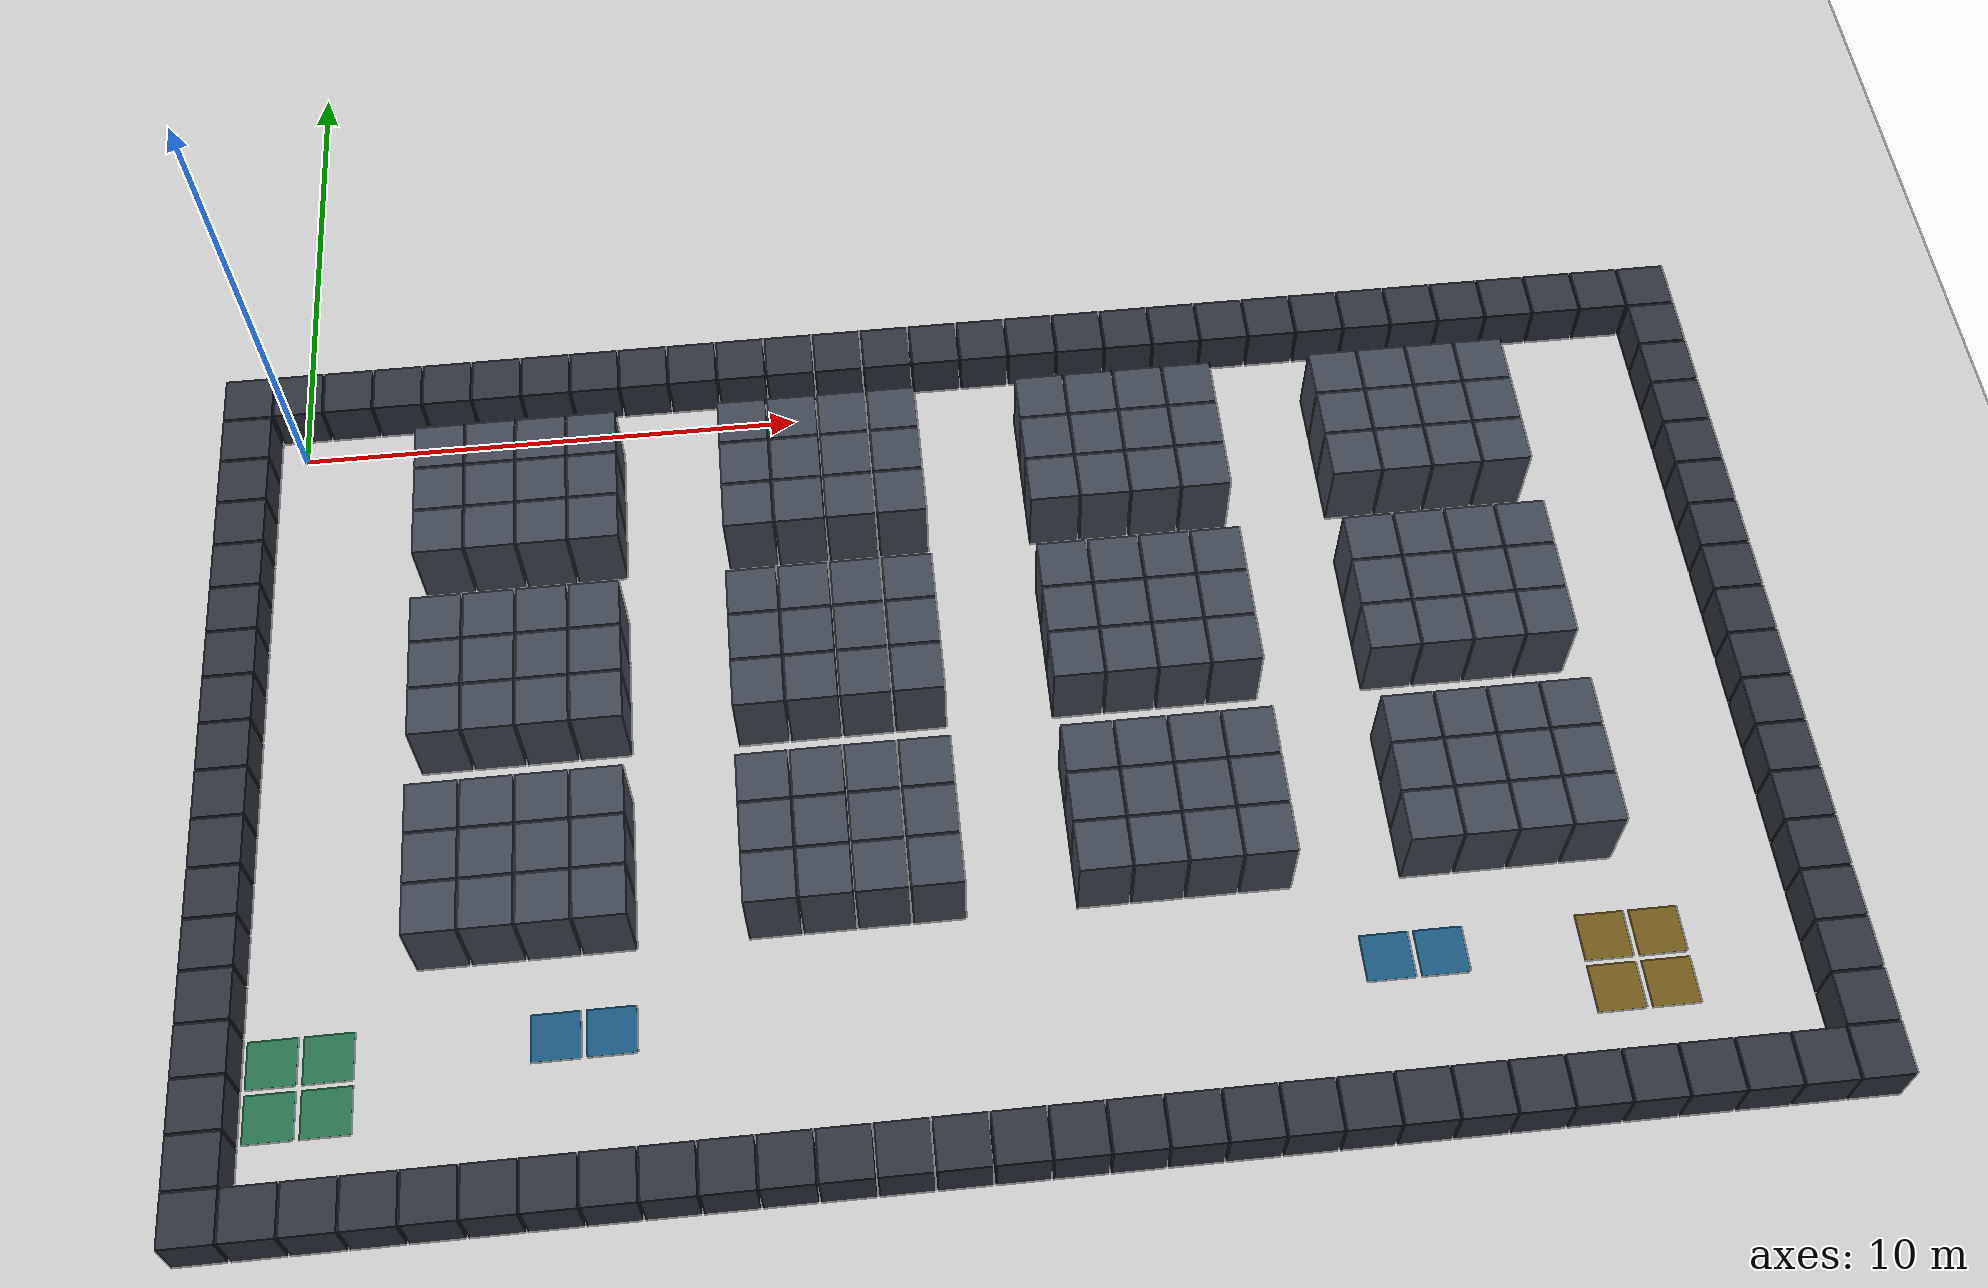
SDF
<?xml version="1.0"?>
<!-- GENERATED by fleet_bringup/scripts/generate_world.py -->
<!-- Do not edit by hand: edit shared/fleetx_core/grid.py and re-run it. -->
<sdf version="1.6">
  <world name="fleetx_warehouse">
    <include><uri>model://sun</uri></include>
    <include><uri>model://ground_plane</uri></include>

    <physics type="ode">
      <max_step_size>0.004</max_step_size>
      <real_time_factor>1.0</real_time_factor>
      <real_time_update_rate>250</real_time_update_rate>
    </physics>

    <scene><ambient>0.6 0.6 0.6 1</ambient><shadows>false</shadows></scene>
    <model name="shelf_3_1">
      <static>true</static>
      <pose>3.000 -1.000 0.800 0 0 0</pose>
      <link name="link">
        <collision name="collision">
          <geometry><box><size>0.960 0.960 1.600</size></box></geometry>
        </collision>
        <visual name="visual">
          <geometry><box><size>0.960 0.960 1.600</size></box></geometry>
          <material><ambient>0.25 0.28 0.33 1</ambient><diffuse>0.25 0.28 0.33 1</diffuse></material>
        </visual>
      </link>
    </model>
    <model name="shelf_4_1">
      <static>true</static>
      <pose>4.000 -1.000 0.800 0 0 0</pose>
      <link name="link">
        <collision name="collision">
          <geometry><box><size>0.960 0.960 1.600</size></box></geometry>
        </collision>
        <visual name="visual">
          <geometry><box><size>0.960 0.960 1.600</size></box></geometry>
          <material><ambient>0.25 0.28 0.33 1</ambient><diffuse>0.25 0.28 0.33 1</diffuse></material>
        </visual>
      </link>
    </model>
    <model name="shelf_5_1">
      <static>true</static>
      <pose>5.000 -1.000 0.800 0 0 0</pose>
      <link name="link">
        <collision name="collision">
          <geometry><box><size>0.960 0.960 1.600</size></box></geometry>
        </collision>
        <visual name="visual">
          <geometry><box><size>0.960 0.960 1.600</size></box></geometry>
          <material><ambient>0.25 0.28 0.33 1</ambient><diffuse>0.25 0.28 0.33 1</diffuse></material>
        </visual>
      </link>
    </model>
    <model name="shelf_6_1">
      <static>true</static>
      <pose>6.000 -1.000 0.800 0 0 0</pose>
      <link name="link">
        <collision name="collision">
          <geometry><box><size>0.960 0.960 1.600</size></box></geometry>
        </collision>
        <visual name="visual">
          <geometry><box><size>0.960 0.960 1.600</size></box></geometry>
          <material><ambient>0.25 0.28 0.33 1</ambient><diffuse>0.25 0.28 0.33 1</diffuse></material>
        </visual>
      </link>
    </model>
    <model name="shelf_9_1">
      <static>true</static>
      <pose>9.000 -1.000 0.800 0 0 0</pose>
      <link name="link">
        <collision name="collision">
          <geometry><box><size>0.960 0.960 1.600</size></box></geometry>
        </collision>
        <visual name="visual">
          <geometry><box><size>0.960 0.960 1.600</size></box></geometry>
          <material><ambient>0.25 0.28 0.33 1</ambient><diffuse>0.25 0.28 0.33 1</diffuse></material>
        </visual>
      </link>
    </model>
    <model name="shelf_10_1">
      <static>true</static>
      <pose>10.000 -1.000 0.800 0 0 0</pose>
      <link name="link">
        <collision name="collision">
          <geometry><box><size>0.960 0.960 1.600</size></box></geometry>
        </collision>
        <visual name="visual">
          <geometry><box><size>0.960 0.960 1.600</size></box></geometry>
          <material><ambient>0.25 0.28 0.33 1</ambient><diffuse>0.25 0.28 0.33 1</diffuse></material>
        </visual>
      </link>
    </model>
    <model name="shelf_11_1">
      <static>true</static>
      <pose>11.000 -1.000 0.800 0 0 0</pose>
      <link name="link">
        <collision name="collision">
          <geometry><box><size>0.960 0.960 1.600</size></box></geometry>
        </collision>
        <visual name="visual">
          <geometry><box><size>0.960 0.960 1.600</size></box></geometry>
          <material><ambient>0.25 0.28 0.33 1</ambient><diffuse>0.25 0.28 0.33 1</diffuse></material>
        </visual>
      </link>
    </model>
    <model name="shelf_12_1">
      <static>true</static>
      <pose>12.000 -1.000 0.800 0 0 0</pose>
      <link name="link">
        <collision name="collision">
          <geometry><box><size>0.960 0.960 1.600</size></box></geometry>
        </collision>
        <visual name="visual">
          <geometry><box><size>0.960 0.960 1.600</size></box></geometry>
          <material><ambient>0.25 0.28 0.33 1</ambient><diffuse>0.25 0.28 0.33 1</diffuse></material>
        </visual>
      </link>
    </model>
    <model name="shelf_15_1">
      <static>true</static>
      <pose>15.000 -1.000 0.800 0 0 0</pose>
      <link name="link">
        <collision name="collision">
          <geometry><box><size>0.960 0.960 1.600</size></box></geometry>
        </collision>
        <visual name="visual">
          <geometry><box><size>0.960 0.960 1.600</size></box></geometry>
          <material><ambient>0.25 0.28 0.33 1</ambient><diffuse>0.25 0.28 0.33 1</diffuse></material>
        </visual>
      </link>
    </model>
    <model name="shelf_16_1">
      <static>true</static>
      <pose>16.000 -1.000 0.800 0 0 0</pose>
      <link name="link">
        <collision name="collision">
          <geometry><box><size>0.960 0.960 1.600</size></box></geometry>
        </collision>
        <visual name="visual">
          <geometry><box><size>0.960 0.960 1.600</size></box></geometry>
          <material><ambient>0.25 0.28 0.33 1</ambient><diffuse>0.25 0.28 0.33 1</diffuse></material>
        </visual>
      </link>
    </model>
    <model name="shelf_17_1">
      <static>true</static>
      <pose>17.000 -1.000 0.800 0 0 0</pose>
      <link name="link">
        <collision name="collision">
          <geometry><box><size>0.960 0.960 1.600</size></box></geometry>
        </collision>
        <visual name="visual">
          <geometry><box><size>0.960 0.960 1.600</size></box></geometry>
          <material><ambient>0.25 0.28 0.33 1</ambient><diffuse>0.25 0.28 0.33 1</diffuse></material>
        </visual>
      </link>
    </model>
    <model name="shelf_18_1">
      <static>true</static>
      <pose>18.000 -1.000 0.800 0 0 0</pose>
      <link name="link">
        <collision name="collision">
          <geometry><box><size>0.960 0.960 1.600</size></box></geometry>
        </collision>
        <visual name="visual">
          <geometry><box><size>0.960 0.960 1.600</size></box></geometry>
          <material><ambient>0.25 0.28 0.33 1</ambient><diffuse>0.25 0.28 0.33 1</diffuse></material>
        </visual>
      </link>
    </model>
    <model name="shelf_21_1">
      <static>true</static>
      <pose>21.000 -1.000 0.800 0 0 0</pose>
      <link name="link">
        <collision name="collision">
          <geometry><box><size>0.960 0.960 1.600</size></box></geometry>
        </collision>
        <visual name="visual">
          <geometry><box><size>0.960 0.960 1.600</size></box></geometry>
          <material><ambient>0.25 0.28 0.33 1</ambient><diffuse>0.25 0.28 0.33 1</diffuse></material>
        </visual>
      </link>
    </model>
    <model name="shelf_22_1">
      <static>true</static>
      <pose>22.000 -1.000 0.800 0 0 0</pose>
      <link name="link">
        <collision name="collision">
          <geometry><box><size>0.960 0.960 1.600</size></box></geometry>
        </collision>
        <visual name="visual">
          <geometry><box><size>0.960 0.960 1.600</size></box></geometry>
          <material><ambient>0.25 0.28 0.33 1</ambient><diffuse>0.25 0.28 0.33 1</diffuse></material>
        </visual>
      </link>
    </model>
    <model name="shelf_23_1">
      <static>true</static>
      <pose>23.000 -1.000 0.800 0 0 0</pose>
      <link name="link">
        <collision name="collision">
          <geometry><box><size>0.960 0.960 1.600</size></box></geometry>
        </collision>
        <visual name="visual">
          <geometry><box><size>0.960 0.960 1.600</size></box></geometry>
          <material><ambient>0.25 0.28 0.33 1</ambient><diffuse>0.25 0.28 0.33 1</diffuse></material>
        </visual>
      </link>
    </model>
    <model name="shelf_24_1">
      <static>true</static>
      <pose>24.000 -1.000 0.800 0 0 0</pose>
      <link name="link">
        <collision name="collision">
          <geometry><box><size>0.960 0.960 1.600</size></box></geometry>
        </collision>
        <visual name="visual">
          <geometry><box><size>0.960 0.960 1.600</size></box></geometry>
          <material><ambient>0.25 0.28 0.33 1</ambient><diffuse>0.25 0.28 0.33 1</diffuse></material>
        </visual>
      </link>
    </model>
    <model name="shelf_3_2">
      <static>true</static>
      <pose>3.000 -2.000 0.800 0 0 0</pose>
      <link name="link">
        <collision name="collision">
          <geometry><box><size>0.960 0.960 1.600</size></box></geometry>
        </collision>
        <visual name="visual">
          <geometry><box><size>0.960 0.960 1.600</size></box></geometry>
          <material><ambient>0.25 0.28 0.33 1</ambient><diffuse>0.25 0.28 0.33 1</diffuse></material>
        </visual>
      </link>
    </model>
    <model name="shelf_4_2">
      <static>true</static>
      <pose>4.000 -2.000 0.800 0 0 0</pose>
      <link name="link">
        <collision name="collision">
          <geometry><box><size>0.960 0.960 1.600</size></box></geometry>
        </collision>
        <visual name="visual">
          <geometry><box><size>0.960 0.960 1.600</size></box></geometry>
          <material><ambient>0.25 0.28 0.33 1</ambient><diffuse>0.25 0.28 0.33 1</diffuse></material>
        </visual>
      </link>
    </model>
    <model name="shelf_5_2">
      <static>true</static>
      <pose>5.000 -2.000 0.800 0 0 0</pose>
      <link name="link">
        <collision name="collision">
          <geometry><box><size>0.960 0.960 1.600</size></box></geometry>
        </collision>
        <visual name="visual">
          <geometry><box><size>0.960 0.960 1.600</size></box></geometry>
          <material><ambient>0.25 0.28 0.33 1</ambient><diffuse>0.25 0.28 0.33 1</diffuse></material>
        </visual>
      </link>
    </model>
    <model name="shelf_6_2">
      <static>true</static>
      <pose>6.000 -2.000 0.800 0 0 0</pose>
      <link name="link">
        <collision name="collision">
          <geometry><box><size>0.960 0.960 1.600</size></box></geometry>
        </collision>
        <visual name="visual">
          <geometry><box><size>0.960 0.960 1.600</size></box></geometry>
          <material><ambient>0.25 0.28 0.33 1</ambient><diffuse>0.25 0.28 0.33 1</diffuse></material>
        </visual>
      </link>
    </model>
    <model name="shelf_9_2">
      <static>true</static>
      <pose>9.000 -2.000 0.800 0 0 0</pose>
      <link name="link">
        <collision name="collision">
          <geometry><box><size>0.960 0.960 1.600</size></box></geometry>
        </collision>
        <visual name="visual">
          <geometry><box><size>0.960 0.960 1.600</size></box></geometry>
          <material><ambient>0.25 0.28 0.33 1</ambient><diffuse>0.25 0.28 0.33 1</diffuse></material>
        </visual>
      </link>
    </model>
    <model name="shelf_10_2">
      <static>true</static>
      <pose>10.000 -2.000 0.800 0 0 0</pose>
      <link name="link">
        <collision name="collision">
          <geometry><box><size>0.960 0.960 1.600</size></box></geometry>
        </collision>
        <visual name="visual">
          <geometry><box><size>0.960 0.960 1.600</size></box></geometry>
          <material><ambient>0.25 0.28 0.33 1</ambient><diffuse>0.25 0.28 0.33 1</diffuse></material>
        </visual>
      </link>
    </model>
    <model name="shelf_11_2">
      <static>true</static>
      <pose>11.000 -2.000 0.800 0 0 0</pose>
      <link name="link">
        <collision name="collision">
          <geometry><box><size>0.960 0.960 1.600</size></box></geometry>
        </collision>
        <visual name="visual">
          <geometry><box><size>0.960 0.960 1.600</size></box></geometry>
          <material><ambient>0.25 0.28 0.33 1</ambient><diffuse>0.25 0.28 0.33 1</diffuse></material>
        </visual>
      </link>
    </model>
    <model name="shelf_12_2">
      <static>true</static>
      <pose>12.000 -2.000 0.800 0 0 0</pose>
      <link name="link">
        <collision name="collision">
          <geometry><box><size>0.960 0.960 1.600</size></box></geometry>
        </collision>
        <visual name="visual">
          <geometry><box><size>0.960 0.960 1.600</size></box></geometry>
          <material><ambient>0.25 0.28 0.33 1</ambient><diffuse>0.25 0.28 0.33 1</diffuse></material>
        </visual>
      </link>
    </model>
    <model name="shelf_15_2">
      <static>true</static>
      <pose>15.000 -2.000 0.800 0 0 0</pose>
      <link name="link">
        <collision name="collision">
          <geometry><box><size>0.960 0.960 1.600</size></box></geometry>
        </collision>
        <visual name="visual">
          <geometry><box><size>0.960 0.960 1.600</size></box></geometry>
          <material><ambient>0.25 0.28 0.33 1</ambient><diffuse>0.25 0.28 0.33 1</diffuse></material>
        </visual>
      </link>
    </model>
    <model name="shelf_16_2">
      <static>true</static>
      <pose>16.000 -2.000 0.800 0 0 0</pose>
      <link name="link">
        <collision name="collision">
          <geometry><box><size>0.960 0.960 1.600</size></box></geometry>
        </collision>
        <visual name="visual">
          <geometry><box><size>0.960 0.960 1.600</size></box></geometry>
          <material><ambient>0.25 0.28 0.33 1</ambient><diffuse>0.25 0.28 0.33 1</diffuse></material>
        </visual>
      </link>
    </model>
    <model name="shelf_17_2">
      <static>true</static>
      <pose>17.000 -2.000 0.800 0 0 0</pose>
      <link name="link">
        <collision name="collision">
          <geometry><box><size>0.960 0.960 1.600</size></box></geometry>
        </collision>
        <visual name="visual">
          <geometry><box><size>0.960 0.960 1.600</size></box></geometry>
          <material><ambient>0.25 0.28 0.33 1</ambient><diffuse>0.25 0.28 0.33 1</diffuse></material>
        </visual>
      </link>
    </model>
    <model name="shelf_18_2">
      <static>true</static>
      <pose>18.000 -2.000 0.800 0 0 0</pose>
      <link name="link">
        <collision name="collision">
          <geometry><box><size>0.960 0.960 1.600</size></box></geometry>
        </collision>
        <visual name="visual">
          <geometry><box><size>0.960 0.960 1.600</size></box></geometry>
          <material><ambient>0.25 0.28 0.33 1</ambient><diffuse>0.25 0.28 0.33 1</diffuse></material>
        </visual>
      </link>
    </model>
    <model name="shelf_21_2">
      <static>true</static>
      <pose>21.000 -2.000 0.800 0 0 0</pose>
      <link name="link">
        <collision name="collision">
          <geometry><box><size>0.960 0.960 1.600</size></box></geometry>
        </collision>
        <visual name="visual">
          <geometry><box><size>0.960 0.960 1.600</size></box></geometry>
          <material><ambient>0.25 0.28 0.33 1</ambient><diffuse>0.25 0.28 0.33 1</diffuse></material>
        </visual>
      </link>
    </model>
    <model name="shelf_22_2">
      <static>true</static>
      <pose>22.000 -2.000 0.800 0 0 0</pose>
      <link name="link">
        <collision name="collision">
          <geometry><box><size>0.960 0.960 1.600</size></box></geometry>
        </collision>
        <visual name="visual">
          <geometry><box><size>0.960 0.960 1.600</size></box></geometry>
          <material><ambient>0.25 0.28 0.33 1</ambient><diffuse>0.25 0.28 0.33 1</diffuse></material>
        </visual>
      </link>
    </model>
    <model name="shelf_23_2">
      <static>true</static>
      <pose>23.000 -2.000 0.800 0 0 0</pose>
      <link name="link">
        <collision name="collision">
          <geometry><box><size>0.960 0.960 1.600</size></box></geometry>
        </collision>
        <visual name="visual">
          <geometry><box><size>0.960 0.960 1.600</size></box></geometry>
          <material><ambient>0.25 0.28 0.33 1</ambient><diffuse>0.25 0.28 0.33 1</diffuse></material>
        </visual>
      </link>
    </model>
    <model name="shelf_24_2">
      <static>true</static>
      <pose>24.000 -2.000 0.800 0 0 0</pose>
      <link name="link">
        <collision name="collision">
          <geometry><box><size>0.960 0.960 1.600</size></box></geometry>
        </collision>
        <visual name="visual">
          <geometry><box><size>0.960 0.960 1.600</size></box></geometry>
          <material><ambient>0.25 0.28 0.33 1</ambient><diffuse>0.25 0.28 0.33 1</diffuse></material>
        </visual>
      </link>
    </model>
    <model name="shelf_3_3">
      <static>true</static>
      <pose>3.000 -3.000 0.800 0 0 0</pose>
      <link name="link">
        <collision name="collision">
          <geometry><box><size>0.960 0.960 1.600</size></box></geometry>
        </collision>
        <visual name="visual">
          <geometry><box><size>0.960 0.960 1.600</size></box></geometry>
          <material><ambient>0.25 0.28 0.33 1</ambient><diffuse>0.25 0.28 0.33 1</diffuse></material>
        </visual>
      </link>
    </model>
    <model name="shelf_4_3">
      <static>true</static>
      <pose>4.000 -3.000 0.800 0 0 0</pose>
      <link name="link">
        <collision name="collision">
          <geometry><box><size>0.960 0.960 1.600</size></box></geometry>
        </collision>
        <visual name="visual">
          <geometry><box><size>0.960 0.960 1.600</size></box></geometry>
          <material><ambient>0.25 0.28 0.33 1</ambient><diffuse>0.25 0.28 0.33 1</diffuse></material>
        </visual>
      </link>
    </model>
    <model name="shelf_5_3">
      <static>true</static>
      <pose>5.000 -3.000 0.800 0 0 0</pose>
      <link name="link">
        <collision name="collision">
          <geometry><box><size>0.960 0.960 1.600</size></box></geometry>
        </collision>
        <visual name="visual">
          <geometry><box><size>0.960 0.960 1.600</size></box></geometry>
          <material><ambient>0.25 0.28 0.33 1</ambient><diffuse>0.25 0.28 0.33 1</diffuse></material>
        </visual>
      </link>
    </model>
    <model name="shelf_6_3">
      <static>true</static>
      <pose>6.000 -3.000 0.800 0 0 0</pose>
      <link name="link">
        <collision name="collision">
          <geometry><box><size>0.960 0.960 1.600</size></box></geometry>
        </collision>
        <visual name="visual">
          <geometry><box><size>0.960 0.960 1.600</size></box></geometry>
          <material><ambient>0.25 0.28 0.33 1</ambient><diffuse>0.25 0.28 0.33 1</diffuse></material>
        </visual>
      </link>
    </model>
    <model name="shelf_9_3">
      <static>true</static>
      <pose>9.000 -3.000 0.800 0 0 0</pose>
      <link name="link">
        <collision name="collision">
          <geometry><box><size>0.960 0.960 1.600</size></box></geometry>
        </collision>
        <visual name="visual">
          <geometry><box><size>0.960 0.960 1.600</size></box></geometry>
          <material><ambient>0.25 0.28 0.33 1</ambient><diffuse>0.25 0.28 0.33 1</diffuse></material>
        </visual>
      </link>
    </model>
    <model name="shelf_10_3">
      <static>true</static>
      <pose>10.000 -3.000 0.800 0 0 0</pose>
      <link name="link">
        <collision name="collision">
          <geometry><box><size>0.960 0.960 1.600</size></box></geometry>
        </collision>
        <visual name="visual">
          <geometry><box><size>0.960 0.960 1.600</size></box></geometry>
          <material><ambient>0.25 0.28 0.33 1</ambient><diffuse>0.25 0.28 0.33 1</diffuse></material>
        </visual>
      </link>
    </model>
    <model name="shelf_11_3">
      <static>true</static>
      <pose>11.000 -3.000 0.800 0 0 0</pose>
      <link name="link">
        <collision name="collision">
          <geometry><box><size>0.960 0.960 1.600</size></box></geometry>
        </collision>
        <visual name="visual">
          <geometry><box><size>0.960 0.960 1.600</size></box></geometry>
          <material><ambient>0.25 0.28 0.33 1</ambient><diffuse>0.25 0.28 0.33 1</diffuse></material>
        </visual>
      </link>
    </model>
    <model name="shelf_12_3">
      <static>true</static>
      <pose>12.000 -3.000 0.800 0 0 0</pose>
      <link name="link">
        <collision name="collision">
          <geometry><box><size>0.960 0.960 1.600</size></box></geometry>
        </collision>
        <visual name="visual">
          <geometry><box><size>0.960 0.960 1.600</size></box></geometry>
          <material><ambient>0.25 0.28 0.33 1</ambient><diffuse>0.25 0.28 0.33 1</diffuse></material>
        </visual>
      </link>
    </model>
    <model name="shelf_15_3">
      <static>true</static>
      <pose>15.000 -3.000 0.800 0 0 0</pose>
      <link name="link">
        <collision name="collision">
          <geometry><box><size>0.960 0.960 1.600</size></box></geometry>
        </collision>
        <visual name="visual">
          <geometry><box><size>0.960 0.960 1.600</size></box></geometry>
          <material><ambient>0.25 0.28 0.33 1</ambient><diffuse>0.25 0.28 0.33 1</diffuse></material>
        </visual>
      </link>
    </model>
    <model name="shelf_16_3">
      <static>true</static>
      <pose>16.000 -3.000 0.800 0 0 0</pose>
      <link name="link">
        <collision name="collision">
          <geometry><box><size>0.960 0.960 1.600</size></box></geometry>
        </collision>
        <visual name="visual">
          <geometry><box><size>0.960 0.960 1.600</size></box></geometry>
          <material><ambient>0.25 0.28 0.33 1</ambient><diffuse>0.25 0.28 0.33 1</diffuse></material>
        </visual>
      </link>
    </model>
    <model name="shelf_17_3">
      <static>true</static>
      <pose>17.000 -3.000 0.800 0 0 0</pose>
      <link name="link">
        <collision name="collision">
          <geometry><box><size>0.960 0.960 1.600</size></box></geometry>
        </collision>
        <visual name="visual">
          <geometry><box><size>0.960 0.960 1.600</size></box></geometry>
          <material><ambient>0.25 0.28 0.33 1</ambient><diffuse>0.25 0.28 0.33 1</diffuse></material>
        </visual>
      </link>
    </model>
    <model name="shelf_18_3">
      <static>true</static>
      <pose>18.000 -3.000 0.800 0 0 0</pose>
      <link name="link">
        <collision name="collision">
          <geometry><box><size>0.960 0.960 1.600</size></box></geometry>
        </collision>
        <visual name="visual">
          <geometry><box><size>0.960 0.960 1.600</size></box></geometry>
          <material><ambient>0.25 0.28 0.33 1</ambient><diffuse>0.25 0.28 0.33 1</diffuse></material>
        </visual>
      </link>
    </model>
    <model name="shelf_21_3">
      <static>true</static>
      <pose>21.000 -3.000 0.800 0 0 0</pose>
      <link name="link">
        <collision name="collision">
          <geometry><box><size>0.960 0.960 1.600</size></box></geometry>
        </collision>
        <visual name="visual">
          <geometry><box><size>0.960 0.960 1.600</size></box></geometry>
          <material><ambient>0.25 0.28 0.33 1</ambient><diffuse>0.25 0.28 0.33 1</diffuse></material>
        </visual>
      </link>
    </model>
    <model name="shelf_22_3">
      <static>true</static>
      <pose>22.000 -3.000 0.800 0 0 0</pose>
      <link name="link">
        <collision name="collision">
          <geometry><box><size>0.960 0.960 1.600</size></box></geometry>
        </collision>
        <visual name="visual">
          <geometry><box><size>0.960 0.960 1.600</size></box></geometry>
          <material><ambient>0.25 0.28 0.33 1</ambient><diffuse>0.25 0.28 0.33 1</diffuse></material>
        </visual>
      </link>
    </model>
    <model name="shelf_23_3">
      <static>true</static>
      <pose>23.000 -3.000 0.800 0 0 0</pose>
      <link name="link">
        <collision name="collision">
          <geometry><box><size>0.960 0.960 1.600</size></box></geometry>
        </collision>
        <visual name="visual">
          <geometry><box><size>0.960 0.960 1.600</size></box></geometry>
          <material><ambient>0.25 0.28 0.33 1</ambient><diffuse>0.25 0.28 0.33 1</diffuse></material>
        </visual>
      </link>
    </model>
    <model name="shelf_24_3">
      <static>true</static>
      <pose>24.000 -3.000 0.800 0 0 0</pose>
      <link name="link">
        <collision name="collision">
          <geometry><box><size>0.960 0.960 1.600</size></box></geometry>
        </collision>
        <visual name="visual">
          <geometry><box><size>0.960 0.960 1.600</size></box></geometry>
          <material><ambient>0.25 0.28 0.33 1</ambient><diffuse>0.25 0.28 0.33 1</diffuse></material>
        </visual>
      </link>
    </model>
    <model name="shelf_3_5">
      <static>true</static>
      <pose>3.000 -5.000 0.800 0 0 0</pose>
      <link name="link">
        <collision name="collision">
          <geometry><box><size>0.960 0.960 1.600</size></box></geometry>
        </collision>
        <visual name="visual">
          <geometry><box><size>0.960 0.960 1.600</size></box></geometry>
          <material><ambient>0.25 0.28 0.33 1</ambient><diffuse>0.25 0.28 0.33 1</diffuse></material>
        </visual>
      </link>
    </model>
    <model name="shelf_4_5">
      <static>true</static>
      <pose>4.000 -5.000 0.800 0 0 0</pose>
      <link name="link">
        <collision name="collision">
          <geometry><box><size>0.960 0.960 1.600</size></box></geometry>
        </collision>
        <visual name="visual">
          <geometry><box><size>0.960 0.960 1.600</size></box></geometry>
          <material><ambient>0.25 0.28 0.33 1</ambient><diffuse>0.25 0.28 0.33 1</diffuse></material>
        </visual>
      </link>
    </model>
    <model name="shelf_5_5">
      <static>true</static>
      <pose>5.000 -5.000 0.800 0 0 0</pose>
      <link name="link">
        <collision name="collision">
          <geometry><box><size>0.960 0.960 1.600</size></box></geometry>
        </collision>
        <visual name="visual">
          <geometry><box><size>0.960 0.960 1.600</size></box></geometry>
          <material><ambient>0.25 0.28 0.33 1</ambient><diffuse>0.25 0.28 0.33 1</diffuse></material>
        </visual>
      </link>
    </model>
    <model name="shelf_6_5">
      <static>true</static>
      <pose>6.000 -5.000 0.800 0 0 0</pose>
      <link name="link">
        <collision name="collision">
          <geometry><box><size>0.960 0.960 1.600</size></box></geometry>
        </collision>
        <visual name="visual">
          <geometry><box><size>0.960 0.960 1.600</size></box></geometry>
          <material><ambient>0.25 0.28 0.33 1</ambient><diffuse>0.25 0.28 0.33 1</diffuse></material>
        </visual>
      </link>
    </model>
    <model name="shelf_9_5">
      <static>true</static>
      <pose>9.000 -5.000 0.800 0 0 0</pose>
      <link name="link">
        <collision name="collision">
          <geometry><box><size>0.960 0.960 1.600</size></box></geometry>
        </collision>
        <visual name="visual">
          <geometry><box><size>0.960 0.960 1.600</size></box></geometry>
          <material><ambient>0.25 0.28 0.33 1</ambient><diffuse>0.25 0.28 0.33 1</diffuse></material>
        </visual>
      </link>
    </model>
    <model name="shelf_10_5">
      <static>true</static>
      <pose>10.000 -5.000 0.800 0 0 0</pose>
      <link name="link">
        <collision name="collision">
          <geometry><box><size>0.960 0.960 1.600</size></box></geometry>
        </collision>
        <visual name="visual">
          <geometry><box><size>0.960 0.960 1.600</size></box></geometry>
          <material><ambient>0.25 0.28 0.33 1</ambient><diffuse>0.25 0.28 0.33 1</diffuse></material>
        </visual>
      </link>
    </model>
    <model name="shelf_11_5">
      <static>true</static>
      <pose>11.000 -5.000 0.800 0 0 0</pose>
      <link name="link">
        <collision name="collision">
          <geometry><box><size>0.960 0.960 1.600</size></box></geometry>
        </collision>
        <visual name="visual">
          <geometry><box><size>0.960 0.960 1.600</size></box></geometry>
          <material><ambient>0.25 0.28 0.33 1</ambient><diffuse>0.25 0.28 0.33 1</diffuse></material>
        </visual>
      </link>
    </model>
    <model name="shelf_12_5">
      <static>true</static>
      <pose>12.000 -5.000 0.800 0 0 0</pose>
      <link name="link">
        <collision name="collision">
          <geometry><box><size>0.960 0.960 1.600</size></box></geometry>
        </collision>
        <visual name="visual">
          <geometry><box><size>0.960 0.960 1.600</size></box></geometry>
          <material><ambient>0.25 0.28 0.33 1</ambient><diffuse>0.25 0.28 0.33 1</diffuse></material>
        </visual>
      </link>
    </model>
    <model name="shelf_15_5">
      <static>true</static>
      <pose>15.000 -5.000 0.800 0 0 0</pose>
      <link name="link">
        <collision name="collision">
          <geometry><box><size>0.960 0.960 1.600</size></box></geometry>
        </collision>
        <visual name="visual">
          <geometry><box><size>0.960 0.960 1.600</size></box></geometry>
          <material><ambient>0.25 0.28 0.33 1</ambient><diffuse>0.25 0.28 0.33 1</diffuse></material>
        </visual>
      </link>
    </model>
    <model name="shelf_16_5">
      <static>true</static>
      <pose>16.000 -5.000 0.800 0 0 0</pose>
      <link name="link">
        <collision name="collision">
          <geometry><box><size>0.960 0.960 1.600</size></box></geometry>
        </collision>
        <visual name="visual">
          <geometry><box><size>0.960 0.960 1.600</size></box></geometry>
          <material><ambient>0.25 0.28 0.33 1</ambient><diffuse>0.25 0.28 0.33 1</diffuse></material>
        </visual>
      </link>
    </model>
    <model name="shelf_17_5">
      <static>true</static>
      <pose>17.000 -5.000 0.800 0 0 0</pose>
      <link name="link">
        <collision name="collision">
          <geometry><box><size>0.960 0.960 1.600</size></box></geometry>
        </collision>
        <visual name="visual">
          <geometry><box><size>0.960 0.960 1.600</size></box></geometry>
          <material><ambient>0.25 0.28 0.33 1</ambient><diffuse>0.25 0.28 0.33 1</diffuse></material>
        </visual>
      </link>
    </model>
    <model name="shelf_18_5">
      <static>true</static>
      <pose>18.000 -5.000 0.800 0 0 0</pose>
      <link name="link">
        <collision name="collision">
          <geometry><box><size>0.960 0.960 1.600</size></box></geometry>
        </collision>
        <visual name="visual">
          <geometry><box><size>0.960 0.960 1.600</size></box></geometry>
          <material><ambient>0.25 0.28 0.33 1</ambient><diffuse>0.25 0.28 0.33 1</diffuse></material>
        </visual>
      </link>
    </model>
    <model name="shelf_21_5">
      <static>true</static>
      <pose>21.000 -5.000 0.800 0 0 0</pose>
      <link name="link">
        <collision name="collision">
          <geometry><box><size>0.960 0.960 1.600</size></box></geometry>
        </collision>
        <visual name="visual">
          <geometry><box><size>0.960 0.960 1.600</size></box></geometry>
          <material><ambient>0.25 0.28 0.33 1</ambient><diffuse>0.25 0.28 0.33 1</diffuse></material>
        </visual>
      </link>
    </model>
    <model name="shelf_22_5">
      <static>true</static>
      <pose>22.000 -5.000 0.800 0 0 0</pose>
      <link name="link">
        <collision name="collision">
          <geometry><box><size>0.960 0.960 1.600</size></box></geometry>
        </collision>
        <visual name="visual">
          <geometry><box><size>0.960 0.960 1.600</size></box></geometry>
          <material><ambient>0.25 0.28 0.33 1</ambient><diffuse>0.25 0.28 0.33 1</diffuse></material>
        </visual>
      </link>
    </model>
    <model name="shelf_23_5">
      <static>true</static>
      <pose>23.000 -5.000 0.800 0 0 0</pose>
      <link name="link">
        <collision name="collision">
          <geometry><box><size>0.960 0.960 1.600</size></box></geometry>
        </collision>
        <visual name="visual">
          <geometry><box><size>0.960 0.960 1.600</size></box></geometry>
          <material><ambient>0.25 0.28 0.33 1</ambient><diffuse>0.25 0.28 0.33 1</diffuse></material>
        </visual>
      </link>
    </model>
    <model name="shelf_24_5">
      <static>true</static>
      <pose>24.000 -5.000 0.800 0 0 0</pose>
      <link name="link">
        <collision name="collision">
          <geometry><box><size>0.960 0.960 1.600</size></box></geometry>
        </collision>
        <visual name="visual">
          <geometry><box><size>0.960 0.960 1.600</size></box></geometry>
          <material><ambient>0.25 0.28 0.33 1</ambient><diffuse>0.25 0.28 0.33 1</diffuse></material>
        </visual>
      </link>
    </model>
    <model name="shelf_3_6">
      <static>true</static>
      <pose>3.000 -6.000 0.800 0 0 0</pose>
      <link name="link">
        <collision name="collision">
          <geometry><box><size>0.960 0.960 1.600</size></box></geometry>
        </collision>
        <visual name="visual">
          <geometry><box><size>0.960 0.960 1.600</size></box></geometry>
          <material><ambient>0.25 0.28 0.33 1</ambient><diffuse>0.25 0.28 0.33 1</diffuse></material>
        </visual>
      </link>
    </model>
    <model name="shelf_4_6">
      <static>true</static>
      <pose>4.000 -6.000 0.800 0 0 0</pose>
      <link name="link">
        <collision name="collision">
          <geometry><box><size>0.960 0.960 1.600</size></box></geometry>
        </collision>
        <visual name="visual">
          <geometry><box><size>0.960 0.960 1.600</size></box></geometry>
          <material><ambient>0.25 0.28 0.33 1</ambient><diffuse>0.25 0.28 0.33 1</diffuse></material>
        </visual>
      </link>
    </model>
    <model name="shelf_5_6">
      <static>true</static>
      <pose>5.000 -6.000 0.800 0 0 0</pose>
      <link name="link">
        <collision name="collision">
          <geometry><box><size>0.960 0.960 1.600</size></box></geometry>
        </collision>
        <visual name="visual">
          <geometry><box><size>0.960 0.960 1.600</size></box></geometry>
          <material><ambient>0.25 0.28 0.33 1</ambient><diffuse>0.25 0.28 0.33 1</diffuse></material>
        </visual>
      </link>
    </model>
    <model name="shelf_6_6">
      <static>true</static>
      <pose>6.000 -6.000 0.800 0 0 0</pose>
      <link name="link">
        <collision name="collision">
          <geometry><box><size>0.960 0.960 1.600</size></box></geometry>
        </collision>
        <visual name="visual">
          <geometry><box><size>0.960 0.960 1.600</size></box></geometry>
          <material><ambient>0.25 0.28 0.33 1</ambient><diffuse>0.25 0.28 0.33 1</diffuse></material>
        </visual>
      </link>
    </model>
    <model name="shelf_9_6">
      <static>true</static>
      <pose>9.000 -6.000 0.800 0 0 0</pose>
      <link name="link">
        <collision name="collision">
          <geometry><box><size>0.960 0.960 1.600</size></box></geometry>
        </collision>
        <visual name="visual">
          <geometry><box><size>0.960 0.960 1.600</size></box></geometry>
          <material><ambient>0.25 0.28 0.33 1</ambient><diffuse>0.25 0.28 0.33 1</diffuse></material>
        </visual>
      </link>
    </model>
    <model name="shelf_10_6">
      <static>true</static>
      <pose>10.000 -6.000 0.800 0 0 0</pose>
      <link name="link">
        <collision name="collision">
          <geometry><box><size>0.960 0.960 1.600</size></box></geometry>
        </collision>
        <visual name="visual">
          <geometry><box><size>0.960 0.960 1.600</size></box></geometry>
          <material><ambient>0.25 0.28 0.33 1</ambient><diffuse>0.25 0.28 0.33 1</diffuse></material>
        </visual>
      </link>
    </model>
    <model name="shelf_11_6">
      <static>true</static>
      <pose>11.000 -6.000 0.800 0 0 0</pose>
      <link name="link">
        <collision name="collision">
          <geometry><box><size>0.960 0.960 1.600</size></box></geometry>
        </collision>
        <visual name="visual">
          <geometry><box><size>0.960 0.960 1.600</size></box></geometry>
          <material><ambient>0.25 0.28 0.33 1</ambient><diffuse>0.25 0.28 0.33 1</diffuse></material>
        </visual>
      </link>
    </model>
    <model name="shelf_12_6">
      <static>true</static>
      <pose>12.000 -6.000 0.800 0 0 0</pose>
      <link name="link">
        <collision name="collision">
          <geometry><box><size>0.960 0.960 1.600</size></box></geometry>
        </collision>
        <visual name="visual">
          <geometry><box><size>0.960 0.960 1.600</size></box></geometry>
          <material><ambient>0.25 0.28 0.33 1</ambient><diffuse>0.25 0.28 0.33 1</diffuse></material>
        </visual>
      </link>
    </model>
    <model name="shelf_15_6">
      <static>true</static>
      <pose>15.000 -6.000 0.800 0 0 0</pose>
      <link name="link">
        <collision name="collision">
          <geometry><box><size>0.960 0.960 1.600</size></box></geometry>
        </collision>
        <visual name="visual">
          <geometry><box><size>0.960 0.960 1.600</size></box></geometry>
          <material><ambient>0.25 0.28 0.33 1</ambient><diffuse>0.25 0.28 0.33 1</diffuse></material>
        </visual>
      </link>
    </model>
    <model name="shelf_16_6">
      <static>true</static>
      <pose>16.000 -6.000 0.800 0 0 0</pose>
      <link name="link">
        <collision name="collision">
          <geometry><box><size>0.960 0.960 1.600</size></box></geometry>
        </collision>
        <visual name="visual">
          <geometry><box><size>0.960 0.960 1.600</size></box></geometry>
          <material><ambient>0.25 0.28 0.33 1</ambient><diffuse>0.25 0.28 0.33 1</diffuse></material>
        </visual>
      </link>
    </model>
    <model name="shelf_17_6">
      <static>true</static>
      <pose>17.000 -6.000 0.800 0 0 0</pose>
      <link name="link">
        <collision name="collision">
          <geometry><box><size>0.960 0.960 1.600</size></box></geometry>
        </collision>
        <visual name="visual">
          <geometry><box><size>0.960 0.960 1.600</size></box></geometry>
          <material><ambient>0.25 0.28 0.33 1</ambient><diffuse>0.25 0.28 0.33 1</diffuse></material>
        </visual>
      </link>
    </model>
    <model name="shelf_18_6">
      <static>true</static>
      <pose>18.000 -6.000 0.800 0 0 0</pose>
      <link name="link">
        <collision name="collision">
          <geometry><box><size>0.960 0.960 1.600</size></box></geometry>
        </collision>
        <visual name="visual">
          <geometry><box><size>0.960 0.960 1.600</size></box></geometry>
          <material><ambient>0.25 0.28 0.33 1</ambient><diffuse>0.25 0.28 0.33 1</diffuse></material>
        </visual>
      </link>
    </model>
    <model name="shelf_21_6">
      <static>true</static>
      <pose>21.000 -6.000 0.800 0 0 0</pose>
      <link name="link">
        <collision name="collision">
          <geometry><box><size>0.960 0.960 1.600</size></box></geometry>
        </collision>
        <visual name="visual">
          <geometry><box><size>0.960 0.960 1.600</size></box></geometry>
          <material><ambient>0.25 0.28 0.33 1</ambient><diffuse>0.25 0.28 0.33 1</diffuse></material>
        </visual>
      </link>
    </model>
    <model name="shelf_22_6">
      <static>true</static>
      <pose>22.000 -6.000 0.800 0 0 0</pose>
      <link name="link">
        <collision name="collision">
          <geometry><box><size>0.960 0.960 1.600</size></box></geometry>
        </collision>
        <visual name="visual">
          <geometry><box><size>0.960 0.960 1.600</size></box></geometry>
          <material><ambient>0.25 0.28 0.33 1</ambient><diffuse>0.25 0.28 0.33 1</diffuse></material>
        </visual>
      </link>
    </model>
    <model name="shelf_23_6">
      <static>true</static>
      <pose>23.000 -6.000 0.800 0 0 0</pose>
      <link name="link">
        <collision name="collision">
          <geometry><box><size>0.960 0.960 1.600</size></box></geometry>
        </collision>
        <visual name="visual">
          <geometry><box><size>0.960 0.960 1.600</size></box></geometry>
          <material><ambient>0.25 0.28 0.33 1</ambient><diffuse>0.25 0.28 0.33 1</diffuse></material>
        </visual>
      </link>
    </model>
    <model name="shelf_24_6">
      <static>true</static>
      <pose>24.000 -6.000 0.800 0 0 0</pose>
      <link name="link">
        <collision name="collision">
          <geometry><box><size>0.960 0.960 1.600</size></box></geometry>
        </collision>
        <visual name="visual">
          <geometry><box><size>0.960 0.960 1.600</size></box></geometry>
          <material><ambient>0.25 0.28 0.33 1</ambient><diffuse>0.25 0.28 0.33 1</diffuse></material>
        </visual>
      </link>
    </model>
    <model name="shelf_3_7">
      <static>true</static>
      <pose>3.000 -7.000 0.800 0 0 0</pose>
      <link name="link">
        <collision name="collision">
          <geometry><box><size>0.960 0.960 1.600</size></box></geometry>
        </collision>
        <visual name="visual">
          <geometry><box><size>0.960 0.960 1.600</size></box></geometry>
          <material><ambient>0.25 0.28 0.33 1</ambient><diffuse>0.25 0.28 0.33 1</diffuse></material>
        </visual>
      </link>
    </model>
    <model name="shelf_4_7">
      <static>true</static>
      <pose>4.000 -7.000 0.800 0 0 0</pose>
      <link name="link">
        <collision name="collision">
          <geometry><box><size>0.960 0.960 1.600</size></box></geometry>
        </collision>
        <visual name="visual">
          <geometry><box><size>0.960 0.960 1.600</size></box></geometry>
          <material><ambient>0.25 0.28 0.33 1</ambient><diffuse>0.25 0.28 0.33 1</diffuse></material>
        </visual>
      </link>
    </model>
    <model name="shelf_5_7">
      <static>true</static>
      <pose>5.000 -7.000 0.800 0 0 0</pose>
      <link name="link">
        <collision name="collision">
          <geometry><box><size>0.960 0.960 1.600</size></box></geometry>
        </collision>
        <visual name="visual">
          <geometry><box><size>0.960 0.960 1.600</size></box></geometry>
          <material><ambient>0.25 0.28 0.33 1</ambient><diffuse>0.25 0.28 0.33 1</diffuse></material>
        </visual>
      </link>
    </model>
    <model name="shelf_6_7">
      <static>true</static>
      <pose>6.000 -7.000 0.800 0 0 0</pose>
      <link name="link">
        <collision name="collision">
          <geometry><box><size>0.960 0.960 1.600</size></box></geometry>
        </collision>
        <visual name="visual">
          <geometry><box><size>0.960 0.960 1.600</size></box></geometry>
          <material><ambient>0.25 0.28 0.33 1</ambient><diffuse>0.25 0.28 0.33 1</diffuse></material>
        </visual>
      </link>
    </model>
    <model name="shelf_9_7">
      <static>true</static>
      <pose>9.000 -7.000 0.800 0 0 0</pose>
      <link name="link">
        <collision name="collision">
          <geometry><box><size>0.960 0.960 1.600</size></box></geometry>
        </collision>
        <visual name="visual">
          <geometry><box><size>0.960 0.960 1.600</size></box></geometry>
          <material><ambient>0.25 0.28 0.33 1</ambient><diffuse>0.25 0.28 0.33 1</diffuse></material>
        </visual>
      </link>
    </model>
    <model name="shelf_10_7">
      <static>true</static>
      <pose>10.000 -7.000 0.800 0 0 0</pose>
      <link name="link">
        <collision name="collision">
          <geometry><box><size>0.960 0.960 1.600</size></box></geometry>
        </collision>
        <visual name="visual">
          <geometry><box><size>0.960 0.960 1.600</size></box></geometry>
          <material><ambient>0.25 0.28 0.33 1</ambient><diffuse>0.25 0.28 0.33 1</diffuse></material>
        </visual>
      </link>
    </model>
    <model name="shelf_11_7">
      <static>true</static>
      <pose>11.000 -7.000 0.800 0 0 0</pose>
      <link name="link">
        <collision name="collision">
          <geometry><box><size>0.960 0.960 1.600</size></box></geometry>
        </collision>
        <visual name="visual">
          <geometry><box><size>0.960 0.960 1.600</size></box></geometry>
          <material><ambient>0.25 0.28 0.33 1</ambient><diffuse>0.25 0.28 0.33 1</diffuse></material>
        </visual>
      </link>
    </model>
    <model name="shelf_12_7">
      <static>true</static>
      <pose>12.000 -7.000 0.800 0 0 0</pose>
      <link name="link">
        <collision name="collision">
          <geometry><box><size>0.960 0.960 1.600</size></box></geometry>
        </collision>
        <visual name="visual">
          <geometry><box><size>0.960 0.960 1.600</size></box></geometry>
          <material><ambient>0.25 0.28 0.33 1</ambient><diffuse>0.25 0.28 0.33 1</diffuse></material>
        </visual>
      </link>
    </model>
    <model name="shelf_15_7">
      <static>true</static>
      <pose>15.000 -7.000 0.800 0 0 0</pose>
      <link name="link">
        <collision name="collision">
          <geometry><box><size>0.960 0.960 1.600</size></box></geometry>
        </collision>
        <visual name="visual">
          <geometry><box><size>0.960 0.960 1.600</size></box></geometry>
          <material><ambient>0.25 0.28 0.33 1</ambient><diffuse>0.25 0.28 0.33 1</diffuse></material>
        </visual>
      </link>
    </model>
    <model name="shelf_16_7">
      <static>true</static>
      <pose>16.000 -7.000 0.800 0 0 0</pose>
      <link name="link">
        <collision name="collision">
          <geometry><box><size>0.960 0.960 1.600</size></box></geometry>
        </collision>
        <visual name="visual">
          <geometry><box><size>0.960 0.960 1.600</size></box></geometry>
          <material><ambient>0.25 0.28 0.33 1</ambient><diffuse>0.25 0.28 0.33 1</diffuse></material>
        </visual>
      </link>
    </model>
    <model name="shelf_17_7">
      <static>true</static>
      <pose>17.000 -7.000 0.800 0 0 0</pose>
      <link name="link">
        <collision name="collision">
          <geometry><box><size>0.960 0.960 1.600</size></box></geometry>
        </collision>
        <visual name="visual">
          <geometry><box><size>0.960 0.960 1.600</size></box></geometry>
          <material><ambient>0.25 0.28 0.33 1</ambient><diffuse>0.25 0.28 0.33 1</diffuse></material>
        </visual>
      </link>
    </model>
    <model name="shelf_18_7">
      <static>true</static>
      <pose>18.000 -7.000 0.800 0 0 0</pose>
      <link name="link">
        <collision name="collision">
          <geometry><box><size>0.960 0.960 1.600</size></box></geometry>
        </collision>
        <visual name="visual">
          <geometry><box><size>0.960 0.960 1.600</size></box></geometry>
          <material><ambient>0.25 0.28 0.33 1</ambient><diffuse>0.25 0.28 0.33 1</diffuse></material>
        </visual>
      </link>
    </model>
    <model name="shelf_21_7">
      <static>true</static>
      <pose>21.000 -7.000 0.800 0 0 0</pose>
      <link name="link">
        <collision name="collision">
          <geometry><box><size>0.960 0.960 1.600</size></box></geometry>
        </collision>
        <visual name="visual">
          <geometry><box><size>0.960 0.960 1.600</size></box></geometry>
          <material><ambient>0.25 0.28 0.33 1</ambient><diffuse>0.25 0.28 0.33 1</diffuse></material>
        </visual>
      </link>
    </model>
    <model name="shelf_22_7">
      <static>true</static>
      <pose>22.000 -7.000 0.800 0 0 0</pose>
      <link name="link">
        <collision name="collision">
          <geometry><box><size>0.960 0.960 1.600</size></box></geometry>
        </collision>
        <visual name="visual">
          <geometry><box><size>0.960 0.960 1.600</size></box></geometry>
          <material><ambient>0.25 0.28 0.33 1</ambient><diffuse>0.25 0.28 0.33 1</diffuse></material>
        </visual>
      </link>
    </model>
    <model name="shelf_23_7">
      <static>true</static>
      <pose>23.000 -7.000 0.800 0 0 0</pose>
      <link name="link">
        <collision name="collision">
          <geometry><box><size>0.960 0.960 1.600</size></box></geometry>
        </collision>
        <visual name="visual">
          <geometry><box><size>0.960 0.960 1.600</size></box></geometry>
          <material><ambient>0.25 0.28 0.33 1</ambient><diffuse>0.25 0.28 0.33 1</diffuse></material>
        </visual>
      </link>
    </model>
    <model name="shelf_24_7">
      <static>true</static>
      <pose>24.000 -7.000 0.800 0 0 0</pose>
      <link name="link">
        <collision name="collision">
          <geometry><box><size>0.960 0.960 1.600</size></box></geometry>
        </collision>
        <visual name="visual">
          <geometry><box><size>0.960 0.960 1.600</size></box></geometry>
          <material><ambient>0.25 0.28 0.33 1</ambient><diffuse>0.25 0.28 0.33 1</diffuse></material>
        </visual>
      </link>
    </model>
    <model name="shelf_3_9">
      <static>true</static>
      <pose>3.000 -9.000 0.800 0 0 0</pose>
      <link name="link">
        <collision name="collision">
          <geometry><box><size>0.960 0.960 1.600</size></box></geometry>
        </collision>
        <visual name="visual">
          <geometry><box><size>0.960 0.960 1.600</size></box></geometry>
          <material><ambient>0.25 0.28 0.33 1</ambient><diffuse>0.25 0.28 0.33 1</diffuse></material>
        </visual>
      </link>
    </model>
    <model name="shelf_4_9">
      <static>true</static>
      <pose>4.000 -9.000 0.800 0 0 0</pose>
      <link name="link">
        <collision name="collision">
          <geometry><box><size>0.960 0.960 1.600</size></box></geometry>
        </collision>
        <visual name="visual">
          <geometry><box><size>0.960 0.960 1.600</size></box></geometry>
          <material><ambient>0.25 0.28 0.33 1</ambient><diffuse>0.25 0.28 0.33 1</diffuse></material>
        </visual>
      </link>
    </model>
    <model name="shelf_5_9">
      <static>true</static>
      <pose>5.000 -9.000 0.800 0 0 0</pose>
      <link name="link">
        <collision name="collision">
          <geometry><box><size>0.960 0.960 1.600</size></box></geometry>
        </collision>
        <visual name="visual">
          <geometry><box><size>0.960 0.960 1.600</size></box></geometry>
          <material><ambient>0.25 0.28 0.33 1</ambient><diffuse>0.25 0.28 0.33 1</diffuse></material>
        </visual>
      </link>
    </model>
    <model name="shelf_6_9">
      <static>true</static>
      <pose>6.000 -9.000 0.800 0 0 0</pose>
      <link name="link">
        <collision name="collision">
          <geometry><box><size>0.960 0.960 1.600</size></box></geometry>
        </collision>
        <visual name="visual">
          <geometry><box><size>0.960 0.960 1.600</size></box></geometry>
          <material><ambient>0.25 0.28 0.33 1</ambient><diffuse>0.25 0.28 0.33 1</diffuse></material>
        </visual>
      </link>
    </model>
    <model name="shelf_9_9">
      <static>true</static>
      <pose>9.000 -9.000 0.800 0 0 0</pose>
      <link name="link">
        <collision name="collision">
          <geometry><box><size>0.960 0.960 1.600</size></box></geometry>
        </collision>
        <visual name="visual">
          <geometry><box><size>0.960 0.960 1.600</size></box></geometry>
          <material><ambient>0.25 0.28 0.33 1</ambient><diffuse>0.25 0.28 0.33 1</diffuse></material>
        </visual>
      </link>
    </model>
    <model name="shelf_10_9">
      <static>true</static>
      <pose>10.000 -9.000 0.800 0 0 0</pose>
      <link name="link">
        <collision name="collision">
          <geometry><box><size>0.960 0.960 1.600</size></box></geometry>
        </collision>
        <visual name="visual">
          <geometry><box><size>0.960 0.960 1.600</size></box></geometry>
          <material><ambient>0.25 0.28 0.33 1</ambient><diffuse>0.25 0.28 0.33 1</diffuse></material>
        </visual>
      </link>
    </model>
    <model name="shelf_11_9">
      <static>true</static>
      <pose>11.000 -9.000 0.800 0 0 0</pose>
      <link name="link">
        <collision name="collision">
          <geometry><box><size>0.960 0.960 1.600</size></box></geometry>
        </collision>
        <visual name="visual">
          <geometry><box><size>0.960 0.960 1.600</size></box></geometry>
          <material><ambient>0.25 0.28 0.33 1</ambient><diffuse>0.25 0.28 0.33 1</diffuse></material>
        </visual>
      </link>
    </model>
    <model name="shelf_12_9">
      <static>true</static>
      <pose>12.000 -9.000 0.800 0 0 0</pose>
      <link name="link">
        <collision name="collision">
          <geometry><box><size>0.960 0.960 1.600</size></box></geometry>
        </collision>
        <visual name="visual">
          <geometry><box><size>0.960 0.960 1.600</size></box></geometry>
          <material><ambient>0.25 0.28 0.33 1</ambient><diffuse>0.25 0.28 0.33 1</diffuse></material>
        </visual>
      </link>
    </model>
    <model name="shelf_15_9">
      <static>true</static>
      <pose>15.000 -9.000 0.800 0 0 0</pose>
      <link name="link">
        <collision name="collision">
          <geometry><box><size>0.960 0.960 1.600</size></box></geometry>
        </collision>
        <visual name="visual">
          <geometry><box><size>0.960 0.960 1.600</size></box></geometry>
          <material><ambient>0.25 0.28 0.33 1</ambient><diffuse>0.25 0.28 0.33 1</diffuse></material>
        </visual>
      </link>
    </model>
    <model name="shelf_16_9">
      <static>true</static>
      <pose>16.000 -9.000 0.800 0 0 0</pose>
      <link name="link">
        <collision name="collision">
          <geometry><box><size>0.960 0.960 1.600</size></box></geometry>
        </collision>
        <visual name="visual">
          <geometry><box><size>0.960 0.960 1.600</size></box></geometry>
          <material><ambient>0.25 0.28 0.33 1</ambient><diffuse>0.25 0.28 0.33 1</diffuse></material>
        </visual>
      </link>
    </model>
    <model name="shelf_17_9">
      <static>true</static>
      <pose>17.000 -9.000 0.800 0 0 0</pose>
      <link name="link">
        <collision name="collision">
          <geometry><box><size>0.960 0.960 1.600</size></box></geometry>
        </collision>
        <visual name="visual">
          <geometry><box><size>0.960 0.960 1.600</size></box></geometry>
          <material><ambient>0.25 0.28 0.33 1</ambient><diffuse>0.25 0.28 0.33 1</diffuse></material>
        </visual>
      </link>
    </model>
    <model name="shelf_18_9">
      <static>true</static>
      <pose>18.000 -9.000 0.800 0 0 0</pose>
      <link name="link">
        <collision name="collision">
          <geometry><box><size>0.960 0.960 1.600</size></box></geometry>
        </collision>
        <visual name="visual">
          <geometry><box><size>0.960 0.960 1.600</size></box></geometry>
          <material><ambient>0.25 0.28 0.33 1</ambient><diffuse>0.25 0.28 0.33 1</diffuse></material>
        </visual>
      </link>
    </model>
    <model name="shelf_21_9">
      <static>true</static>
      <pose>21.000 -9.000 0.800 0 0 0</pose>
      <link name="link">
        <collision name="collision">
          <geometry><box><size>0.960 0.960 1.600</size></box></geometry>
        </collision>
        <visual name="visual">
          <geometry><box><size>0.960 0.960 1.600</size></box></geometry>
          <material><ambient>0.25 0.28 0.33 1</ambient><diffuse>0.25 0.28 0.33 1</diffuse></material>
        </visual>
      </link>
    </model>
    <model name="shelf_22_9">
      <static>true</static>
      <pose>22.000 -9.000 0.800 0 0 0</pose>
      <link name="link">
        <collision name="collision">
          <geometry><box><size>0.960 0.960 1.600</size></box></geometry>
        </collision>
        <visual name="visual">
          <geometry><box><size>0.960 0.960 1.600</size></box></geometry>
          <material><ambient>0.25 0.28 0.33 1</ambient><diffuse>0.25 0.28 0.33 1</diffuse></material>
        </visual>
      </link>
    </model>
    <model name="shelf_23_9">
      <static>true</static>
      <pose>23.000 -9.000 0.800 0 0 0</pose>
      <link name="link">
        <collision name="collision">
          <geometry><box><size>0.960 0.960 1.600</size></box></geometry>
        </collision>
        <visual name="visual">
          <geometry><box><size>0.960 0.960 1.600</size></box></geometry>
          <material><ambient>0.25 0.28 0.33 1</ambient><diffuse>0.25 0.28 0.33 1</diffuse></material>
        </visual>
      </link>
    </model>
    <model name="shelf_24_9">
      <static>true</static>
      <pose>24.000 -9.000 0.800 0 0 0</pose>
      <link name="link">
        <collision name="collision">
          <geometry><box><size>0.960 0.960 1.600</size></box></geometry>
        </collision>
        <visual name="visual">
          <geometry><box><size>0.960 0.960 1.600</size></box></geometry>
          <material><ambient>0.25 0.28 0.33 1</ambient><diffuse>0.25 0.28 0.33 1</diffuse></material>
        </visual>
      </link>
    </model>
    <model name="shelf_3_10">
      <static>true</static>
      <pose>3.000 -10.000 0.800 0 0 0</pose>
      <link name="link">
        <collision name="collision">
          <geometry><box><size>0.960 0.960 1.600</size></box></geometry>
        </collision>
        <visual name="visual">
          <geometry><box><size>0.960 0.960 1.600</size></box></geometry>
          <material><ambient>0.25 0.28 0.33 1</ambient><diffuse>0.25 0.28 0.33 1</diffuse></material>
        </visual>
      </link>
    </model>
    <model name="shelf_4_10">
      <static>true</static>
      <pose>4.000 -10.000 0.800 0 0 0</pose>
      <link name="link">
        <collision name="collision">
          <geometry><box><size>0.960 0.960 1.600</size></box></geometry>
        </collision>
        <visual name="visual">
          <geometry><box><size>0.960 0.960 1.600</size></box></geometry>
          <material><ambient>0.25 0.28 0.33 1</ambient><diffuse>0.25 0.28 0.33 1</diffuse></material>
        </visual>
      </link>
    </model>
    <model name="shelf_5_10">
      <static>true</static>
      <pose>5.000 -10.000 0.800 0 0 0</pose>
      <link name="link">
        <collision name="collision">
          <geometry><box><size>0.960 0.960 1.600</size></box></geometry>
        </collision>
        <visual name="visual">
          <geometry><box><size>0.960 0.960 1.600</size></box></geometry>
          <material><ambient>0.25 0.28 0.33 1</ambient><diffuse>0.25 0.28 0.33 1</diffuse></material>
        </visual>
      </link>
    </model>
    <model name="shelf_6_10">
      <static>true</static>
      <pose>6.000 -10.000 0.800 0 0 0</pose>
      <link name="link">
        <collision name="collision">
          <geometry><box><size>0.960 0.960 1.600</size></box></geometry>
        </collision>
        <visual name="visual">
          <geometry><box><size>0.960 0.960 1.600</size></box></geometry>
          <material><ambient>0.25 0.28 0.33 1</ambient><diffuse>0.25 0.28 0.33 1</diffuse></material>
        </visual>
      </link>
    </model>
    <model name="shelf_9_10">
      <static>true</static>
      <pose>9.000 -10.000 0.800 0 0 0</pose>
      <link name="link">
        <collision name="collision">
          <geometry><box><size>0.960 0.960 1.600</size></box></geometry>
        </collision>
        <visual name="visual">
          <geometry><box><size>0.960 0.960 1.600</size></box></geometry>
          <material><ambient>0.25 0.28 0.33 1</ambient><diffuse>0.25 0.28 0.33 1</diffuse></material>
        </visual>
      </link>
    </model>
    <model name="shelf_10_10">
      <static>true</static>
      <pose>10.000 -10.000 0.800 0 0 0</pose>
      <link name="link">
        <collision name="collision">
          <geometry><box><size>0.960 0.960 1.600</size></box></geometry>
        </collision>
        <visual name="visual">
          <geometry><box><size>0.960 0.960 1.600</size></box></geometry>
          <material><ambient>0.25 0.28 0.33 1</ambient><diffuse>0.25 0.28 0.33 1</diffuse></material>
        </visual>
      </link>
    </model>
    <model name="shelf_11_10">
      <static>true</static>
      <pose>11.000 -10.000 0.800 0 0 0</pose>
      <link name="link">
        <collision name="collision">
          <geometry><box><size>0.960 0.960 1.600</size></box></geometry>
        </collision>
        <visual name="visual">
          <geometry><box><size>0.960 0.960 1.600</size></box></geometry>
          <material><ambient>0.25 0.28 0.33 1</ambient><diffuse>0.25 0.28 0.33 1</diffuse></material>
        </visual>
      </link>
    </model>
    <model name="shelf_12_10">
      <static>true</static>
      <pose>12.000 -10.000 0.800 0 0 0</pose>
      <link name="link">
        <collision name="collision">
          <geometry><box><size>0.960 0.960 1.600</size></box></geometry>
        </collision>
        <visual name="visual">
          <geometry><box><size>0.960 0.960 1.600</size></box></geometry>
          <material><ambient>0.25 0.28 0.33 1</ambient><diffuse>0.25 0.28 0.33 1</diffuse></material>
        </visual>
      </link>
    </model>
    <model name="shelf_15_10">
      <static>true</static>
      <pose>15.000 -10.000 0.800 0 0 0</pose>
      <link name="link">
        <collision name="collision">
          <geometry><box><size>0.960 0.960 1.600</size></box></geometry>
        </collision>
        <visual name="visual">
          <geometry><box><size>0.960 0.960 1.600</size></box></geometry>
          <material><ambient>0.25 0.28 0.33 1</ambient><diffuse>0.25 0.28 0.33 1</diffuse></material>
        </visual>
      </link>
    </model>
    <model name="shelf_16_10">
      <static>true</static>
      <pose>16.000 -10.000 0.800 0 0 0</pose>
      <link name="link">
        <collision name="collision">
          <geometry><box><size>0.960 0.960 1.600</size></box></geometry>
        </collision>
        <visual name="visual">
          <geometry><box><size>0.960 0.960 1.600</size></box></geometry>
          <material><ambient>0.25 0.28 0.33 1</ambient><diffuse>0.25 0.28 0.33 1</diffuse></material>
        </visual>
      </link>
    </model>
    <model name="shelf_17_10">
      <static>true</static>
      <pose>17.000 -10.000 0.800 0 0 0</pose>
      <link name="link">
        <collision name="collision">
          <geometry><box><size>0.960 0.960 1.600</size></box></geometry>
        </collision>
        <visual name="visual">
          <geometry><box><size>0.960 0.960 1.600</size></box></geometry>
          <material><ambient>0.25 0.28 0.33 1</ambient><diffuse>0.25 0.28 0.33 1</diffuse></material>
        </visual>
      </link>
    </model>
    <model name="shelf_18_10">
      <static>true</static>
      <pose>18.000 -10.000 0.800 0 0 0</pose>
      <link name="link">
        <collision name="collision">
          <geometry><box><size>0.960 0.960 1.600</size></box></geometry>
        </collision>
        <visual name="visual">
          <geometry><box><size>0.960 0.960 1.600</size></box></geometry>
          <material><ambient>0.25 0.28 0.33 1</ambient><diffuse>0.25 0.28 0.33 1</diffuse></material>
        </visual>
      </link>
    </model>
    <model name="shelf_21_10">
      <static>true</static>
      <pose>21.000 -10.000 0.800 0 0 0</pose>
      <link name="link">
        <collision name="collision">
          <geometry><box><size>0.960 0.960 1.600</size></box></geometry>
        </collision>
        <visual name="visual">
          <geometry><box><size>0.960 0.960 1.600</size></box></geometry>
          <material><ambient>0.25 0.28 0.33 1</ambient><diffuse>0.25 0.28 0.33 1</diffuse></material>
        </visual>
      </link>
    </model>
    <model name="shelf_22_10">
      <static>true</static>
      <pose>22.000 -10.000 0.800 0 0 0</pose>
      <link name="link">
        <collision name="collision">
          <geometry><box><size>0.960 0.960 1.600</size></box></geometry>
        </collision>
        <visual name="visual">
          <geometry><box><size>0.960 0.960 1.600</size></box></geometry>
          <material><ambient>0.25 0.28 0.33 1</ambient><diffuse>0.25 0.28 0.33 1</diffuse></material>
        </visual>
      </link>
    </model>
    <model name="shelf_23_10">
      <static>true</static>
      <pose>23.000 -10.000 0.800 0 0 0</pose>
      <link name="link">
        <collision name="collision">
          <geometry><box><size>0.960 0.960 1.600</size></box></geometry>
        </collision>
        <visual name="visual">
          <geometry><box><size>0.960 0.960 1.600</size></box></geometry>
          <material><ambient>0.25 0.28 0.33 1</ambient><diffuse>0.25 0.28 0.33 1</diffuse></material>
        </visual>
      </link>
    </model>
    <model name="shelf_24_10">
      <static>true</static>
      <pose>24.000 -10.000 0.800 0 0 0</pose>
      <link name="link">
        <collision name="collision">
          <geometry><box><size>0.960 0.960 1.600</size></box></geometry>
        </collision>
        <visual name="visual">
          <geometry><box><size>0.960 0.960 1.600</size></box></geometry>
          <material><ambient>0.25 0.28 0.33 1</ambient><diffuse>0.25 0.28 0.33 1</diffuse></material>
        </visual>
      </link>
    </model>
    <model name="shelf_3_11">
      <static>true</static>
      <pose>3.000 -11.000 0.800 0 0 0</pose>
      <link name="link">
        <collision name="collision">
          <geometry><box><size>0.960 0.960 1.600</size></box></geometry>
        </collision>
        <visual name="visual">
          <geometry><box><size>0.960 0.960 1.600</size></box></geometry>
          <material><ambient>0.25 0.28 0.33 1</ambient><diffuse>0.25 0.28 0.33 1</diffuse></material>
        </visual>
      </link>
    </model>
    <model name="shelf_4_11">
      <static>true</static>
      <pose>4.000 -11.000 0.800 0 0 0</pose>
      <link name="link">
        <collision name="collision">
          <geometry><box><size>0.960 0.960 1.600</size></box></geometry>
        </collision>
        <visual name="visual">
          <geometry><box><size>0.960 0.960 1.600</size></box></geometry>
          <material><ambient>0.25 0.28 0.33 1</ambient><diffuse>0.25 0.28 0.33 1</diffuse></material>
        </visual>
      </link>
    </model>
    <model name="shelf_5_11">
      <static>true</static>
      <pose>5.000 -11.000 0.800 0 0 0</pose>
      <link name="link">
        <collision name="collision">
          <geometry><box><size>0.960 0.960 1.600</size></box></geometry>
        </collision>
        <visual name="visual">
          <geometry><box><size>0.960 0.960 1.600</size></box></geometry>
          <material><ambient>0.25 0.28 0.33 1</ambient><diffuse>0.25 0.28 0.33 1</diffuse></material>
        </visual>
      </link>
    </model>
    <model name="shelf_6_11">
      <static>true</static>
      <pose>6.000 -11.000 0.800 0 0 0</pose>
      <link name="link">
        <collision name="collision">
          <geometry><box><size>0.960 0.960 1.600</size></box></geometry>
        </collision>
        <visual name="visual">
          <geometry><box><size>0.960 0.960 1.600</size></box></geometry>
          <material><ambient>0.25 0.28 0.33 1</ambient><diffuse>0.25 0.28 0.33 1</diffuse></material>
        </visual>
      </link>
    </model>
    <model name="shelf_9_11">
      <static>true</static>
      <pose>9.000 -11.000 0.800 0 0 0</pose>
      <link name="link">
        <collision name="collision">
          <geometry><box><size>0.960 0.960 1.600</size></box></geometry>
        </collision>
        <visual name="visual">
          <geometry><box><size>0.960 0.960 1.600</size></box></geometry>
          <material><ambient>0.25 0.28 0.33 1</ambient><diffuse>0.25 0.28 0.33 1</diffuse></material>
        </visual>
      </link>
    </model>
    <model name="shelf_10_11">
      <static>true</static>
      <pose>10.000 -11.000 0.800 0 0 0</pose>
      <link name="link">
        <collision name="collision">
          <geometry><box><size>0.960 0.960 1.600</size></box></geometry>
        </collision>
        <visual name="visual">
          <geometry><box><size>0.960 0.960 1.600</size></box></geometry>
          <material><ambient>0.25 0.28 0.33 1</ambient><diffuse>0.25 0.28 0.33 1</diffuse></material>
        </visual>
      </link>
    </model>
    <model name="shelf_11_11">
      <static>true</static>
      <pose>11.000 -11.000 0.800 0 0 0</pose>
      <link name="link">
        <collision name="collision">
          <geometry><box><size>0.960 0.960 1.600</size></box></geometry>
        </collision>
        <visual name="visual">
          <geometry><box><size>0.960 0.960 1.600</size></box></geometry>
          <material><ambient>0.25 0.28 0.33 1</ambient><diffuse>0.25 0.28 0.33 1</diffuse></material>
        </visual>
      </link>
    </model>
    <model name="shelf_12_11">
      <static>true</static>
      <pose>12.000 -11.000 0.800 0 0 0</pose>
      <link name="link">
        <collision name="collision">
          <geometry><box><size>0.960 0.960 1.600</size></box></geometry>
        </collision>
        <visual name="visual">
          <geometry><box><size>0.960 0.960 1.600</size></box></geometry>
          <material><ambient>0.25 0.28 0.33 1</ambient><diffuse>0.25 0.28 0.33 1</diffuse></material>
        </visual>
      </link>
    </model>
    <model name="shelf_15_11">
      <static>true</static>
      <pose>15.000 -11.000 0.800 0 0 0</pose>
      <link name="link">
        <collision name="collision">
          <geometry><box><size>0.960 0.960 1.600</size></box></geometry>
        </collision>
        <visual name="visual">
          <geometry><box><size>0.960 0.960 1.600</size></box></geometry>
          <material><ambient>0.25 0.28 0.33 1</ambient><diffuse>0.25 0.28 0.33 1</diffuse></material>
        </visual>
      </link>
    </model>
    <model name="shelf_16_11">
      <static>true</static>
      <pose>16.000 -11.000 0.800 0 0 0</pose>
      <link name="link">
        <collision name="collision">
          <geometry><box><size>0.960 0.960 1.600</size></box></geometry>
        </collision>
        <visual name="visual">
          <geometry><box><size>0.960 0.960 1.600</size></box></geometry>
          <material><ambient>0.25 0.28 0.33 1</ambient><diffuse>0.25 0.28 0.33 1</diffuse></material>
        </visual>
      </link>
    </model>
    <model name="shelf_17_11">
      <static>true</static>
      <pose>17.000 -11.000 0.800 0 0 0</pose>
      <link name="link">
        <collision name="collision">
          <geometry><box><size>0.960 0.960 1.600</size></box></geometry>
        </collision>
        <visual name="visual">
          <geometry><box><size>0.960 0.960 1.600</size></box></geometry>
          <material><ambient>0.25 0.28 0.33 1</ambient><diffuse>0.25 0.28 0.33 1</diffuse></material>
        </visual>
      </link>
    </model>
    <model name="shelf_18_11">
      <static>true</static>
      <pose>18.000 -11.000 0.800 0 0 0</pose>
      <link name="link">
        <collision name="collision">
          <geometry><box><size>0.960 0.960 1.600</size></box></geometry>
        </collision>
        <visual name="visual">
          <geometry><box><size>0.960 0.960 1.600</size></box></geometry>
          <material><ambient>0.25 0.28 0.33 1</ambient><diffuse>0.25 0.28 0.33 1</diffuse></material>
        </visual>
      </link>
    </model>
    <model name="shelf_21_11">
      <static>true</static>
      <pose>21.000 -11.000 0.800 0 0 0</pose>
      <link name="link">
        <collision name="collision">
          <geometry><box><size>0.960 0.960 1.600</size></box></geometry>
        </collision>
        <visual name="visual">
          <geometry><box><size>0.960 0.960 1.600</size></box></geometry>
          <material><ambient>0.25 0.28 0.33 1</ambient><diffuse>0.25 0.28 0.33 1</diffuse></material>
        </visual>
      </link>
    </model>
    <model name="shelf_22_11">
      <static>true</static>
      <pose>22.000 -11.000 0.800 0 0 0</pose>
      <link name="link">
        <collision name="collision">
          <geometry><box><size>0.960 0.960 1.600</size></box></geometry>
        </collision>
        <visual name="visual">
          <geometry><box><size>0.960 0.960 1.600</size></box></geometry>
          <material><ambient>0.25 0.28 0.33 1</ambient><diffuse>0.25 0.28 0.33 1</diffuse></material>
        </visual>
      </link>
    </model>
    <model name="shelf_23_11">
      <static>true</static>
      <pose>23.000 -11.000 0.800 0 0 0</pose>
      <link name="link">
        <collision name="collision">
          <geometry><box><size>0.960 0.960 1.600</size></box></geometry>
        </collision>
        <visual name="visual">
          <geometry><box><size>0.960 0.960 1.600</size></box></geometry>
          <material><ambient>0.25 0.28 0.33 1</ambient><diffuse>0.25 0.28 0.33 1</diffuse></material>
        </visual>
      </link>
    </model>
    <model name="shelf_24_11">
      <static>true</static>
      <pose>24.000 -11.000 0.800 0 0 0</pose>
      <link name="link">
        <collision name="collision">
          <geometry><box><size>0.960 0.960 1.600</size></box></geometry>
        </collision>
        <visual name="visual">
          <geometry><box><size>0.960 0.960 1.600</size></box></geometry>
          <material><ambient>0.25 0.28 0.33 1</ambient><diffuse>0.25 0.28 0.33 1</diffuse></material>
        </visual>
      </link>
    </model>
    <model name="pick_0_13">
      <static>true</static>
      <pose>0.000 -13.000 0.005 0 0 0</pose>
      <link name="link">
        <visual name="visual">
          <geometry><box><size>0.900 0.900 0.01</size></box></geometry>
          <material><ambient>0.15 0.45 0.30 1</ambient><diffuse>0.15 0.45 0.30 1</diffuse></material>
        </visual>
      </link>
    </model>
    <model name="pick_1_13">
      <static>true</static>
      <pose>1.000 -13.000 0.005 0 0 0</pose>
      <link name="link">
        <visual name="visual">
          <geometry><box><size>0.900 0.900 0.01</size></box></geometry>
          <material><ambient>0.15 0.45 0.30 1</ambient><diffuse>0.15 0.45 0.30 1</diffuse></material>
        </visual>
      </link>
    </model>
    <model name="drop_5_13">
      <static>true</static>
      <pose>5.000 -13.000 0.005 0 0 0</pose>
      <link name="link">
        <visual name="visual">
          <geometry><box><size>0.900 0.900 0.01</size></box></geometry>
          <material><ambient>0.10 0.35 0.50 1</ambient><diffuse>0.10 0.35 0.50 1</diffuse></material>
        </visual>
      </link>
    </model>
    <model name="drop_6_13">
      <static>true</static>
      <pose>6.000 -13.000 0.005 0 0 0</pose>
      <link name="link">
        <visual name="visual">
          <geometry><box><size>0.900 0.900 0.01</size></box></geometry>
          <material><ambient>0.10 0.35 0.50 1</ambient><diffuse>0.10 0.35 0.50 1</diffuse></material>
        </visual>
      </link>
    </model>
    <model name="drop_20_13">
      <static>true</static>
      <pose>20.000 -13.000 0.005 0 0 0</pose>
      <link name="link">
        <visual name="visual">
          <geometry><box><size>0.900 0.900 0.01</size></box></geometry>
          <material><ambient>0.10 0.35 0.50 1</ambient><diffuse>0.10 0.35 0.50 1</diffuse></material>
        </visual>
      </link>
    </model>
    <model name="drop_21_13">
      <static>true</static>
      <pose>21.000 -13.000 0.005 0 0 0</pose>
      <link name="link">
        <visual name="visual">
          <geometry><box><size>0.900 0.900 0.01</size></box></geometry>
          <material><ambient>0.10 0.35 0.50 1</ambient><diffuse>0.10 0.35 0.50 1</diffuse></material>
        </visual>
      </link>
    </model>
    <model name="charger_24_13">
      <static>true</static>
      <pose>24.000 -13.000 0.005 0 0 0</pose>
      <link name="link">
        <visual name="visual">
          <geometry><box><size>0.900 0.900 0.01</size></box></geometry>
          <material><ambient>0.45 0.35 0.10 1</ambient><diffuse>0.45 0.35 0.10 1</diffuse></material>
        </visual>
      </link>
    </model>
    <model name="charger_25_13">
      <static>true</static>
      <pose>25.000 -13.000 0.005 0 0 0</pose>
      <link name="link">
        <visual name="visual">
          <geometry><box><size>0.900 0.900 0.01</size></box></geometry>
          <material><ambient>0.45 0.35 0.10 1</ambient><diffuse>0.45 0.35 0.10 1</diffuse></material>
        </visual>
      </link>
    </model>
    <model name="pick_0_14">
      <static>true</static>
      <pose>0.000 -14.000 0.005 0 0 0</pose>
      <link name="link">
        <visual name="visual">
          <geometry><box><size>0.900 0.900 0.01</size></box></geometry>
          <material><ambient>0.15 0.45 0.30 1</ambient><diffuse>0.15 0.45 0.30 1</diffuse></material>
        </visual>
      </link>
    </model>
    <model name="pick_1_14">
      <static>true</static>
      <pose>1.000 -14.000 0.005 0 0 0</pose>
      <link name="link">
        <visual name="visual">
          <geometry><box><size>0.900 0.900 0.01</size></box></geometry>
          <material><ambient>0.15 0.45 0.30 1</ambient><diffuse>0.15 0.45 0.30 1</diffuse></material>
        </visual>
      </link>
    </model>
    <model name="charger_24_14">
      <static>true</static>
      <pose>24.000 -14.000 0.005 0 0 0</pose>
      <link name="link">
        <visual name="visual">
          <geometry><box><size>0.900 0.900 0.01</size></box></geometry>
          <material><ambient>0.45 0.35 0.10 1</ambient><diffuse>0.45 0.35 0.10 1</diffuse></material>
        </visual>
      </link>
    </model>
    <model name="charger_25_14">
      <static>true</static>
      <pose>25.000 -14.000 0.005 0 0 0</pose>
      <link name="link">
        <visual name="visual">
          <geometry><box><size>0.900 0.900 0.01</size></box></geometry>
          <material><ambient>0.45 0.35 0.10 1</ambient><diffuse>0.45 0.35 0.10 1</diffuse></material>
        </visual>
      </link>
    </model>
    <model name="wall_n_-1">
      <static>true</static>
      <pose>-1.000 1.000 0.500 0 0 0</pose>
      <link name="link">
        <collision name="collision">
          <geometry><box><size>0.960 0.960 1.000</size></box></geometry>
        </collision>
        <visual name="visual">
          <geometry><box><size>0.960 0.960 1.000</size></box></geometry>
          <material><ambient>0.18 0.20 0.24 1</ambient><diffuse>0.18 0.20 0.24 1</diffuse></material>
        </visual>
      </link>
    </model>
    <model name="wall_s_-1">
      <static>true</static>
      <pose>-1.000 -16.000 0.500 0 0 0</pose>
      <link name="link">
        <collision name="collision">
          <geometry><box><size>0.960 0.960 1.000</size></box></geometry>
        </collision>
        <visual name="visual">
          <geometry><box><size>0.960 0.960 1.000</size></box></geometry>
          <material><ambient>0.18 0.20 0.24 1</ambient><diffuse>0.18 0.20 0.24 1</diffuse></material>
        </visual>
      </link>
    </model>
    <model name="wall_n_0">
      <static>true</static>
      <pose>0.000 1.000 0.500 0 0 0</pose>
      <link name="link">
        <collision name="collision">
          <geometry><box><size>0.960 0.960 1.000</size></box></geometry>
        </collision>
        <visual name="visual">
          <geometry><box><size>0.960 0.960 1.000</size></box></geometry>
          <material><ambient>0.18 0.20 0.24 1</ambient><diffuse>0.18 0.20 0.24 1</diffuse></material>
        </visual>
      </link>
    </model>
    <model name="wall_s_0">
      <static>true</static>
      <pose>0.000 -16.000 0.500 0 0 0</pose>
      <link name="link">
        <collision name="collision">
          <geometry><box><size>0.960 0.960 1.000</size></box></geometry>
        </collision>
        <visual name="visual">
          <geometry><box><size>0.960 0.960 1.000</size></box></geometry>
          <material><ambient>0.18 0.20 0.24 1</ambient><diffuse>0.18 0.20 0.24 1</diffuse></material>
        </visual>
      </link>
    </model>
    <model name="wall_n_1">
      <static>true</static>
      <pose>1.000 1.000 0.500 0 0 0</pose>
      <link name="link">
        <collision name="collision">
          <geometry><box><size>0.960 0.960 1.000</size></box></geometry>
        </collision>
        <visual name="visual">
          <geometry><box><size>0.960 0.960 1.000</size></box></geometry>
          <material><ambient>0.18 0.20 0.24 1</ambient><diffuse>0.18 0.20 0.24 1</diffuse></material>
        </visual>
      </link>
    </model>
    <model name="wall_s_1">
      <static>true</static>
      <pose>1.000 -16.000 0.500 0 0 0</pose>
      <link name="link">
        <collision name="collision">
          <geometry><box><size>0.960 0.960 1.000</size></box></geometry>
        </collision>
        <visual name="visual">
          <geometry><box><size>0.960 0.960 1.000</size></box></geometry>
          <material><ambient>0.18 0.20 0.24 1</ambient><diffuse>0.18 0.20 0.24 1</diffuse></material>
        </visual>
      </link>
    </model>
    <model name="wall_n_2">
      <static>true</static>
      <pose>2.000 1.000 0.500 0 0 0</pose>
      <link name="link">
        <collision name="collision">
          <geometry><box><size>0.960 0.960 1.000</size></box></geometry>
        </collision>
        <visual name="visual">
          <geometry><box><size>0.960 0.960 1.000</size></box></geometry>
          <material><ambient>0.18 0.20 0.24 1</ambient><diffuse>0.18 0.20 0.24 1</diffuse></material>
        </visual>
      </link>
    </model>
    <model name="wall_s_2">
      <static>true</static>
      <pose>2.000 -16.000 0.500 0 0 0</pose>
      <link name="link">
        <collision name="collision">
          <geometry><box><size>0.960 0.960 1.000</size></box></geometry>
        </collision>
        <visual name="visual">
          <geometry><box><size>0.960 0.960 1.000</size></box></geometry>
          <material><ambient>0.18 0.20 0.24 1</ambient><diffuse>0.18 0.20 0.24 1</diffuse></material>
        </visual>
      </link>
    </model>
    <model name="wall_n_3">
      <static>true</static>
      <pose>3.000 1.000 0.500 0 0 0</pose>
      <link name="link">
        <collision name="collision">
          <geometry><box><size>0.960 0.960 1.000</size></box></geometry>
        </collision>
        <visual name="visual">
          <geometry><box><size>0.960 0.960 1.000</size></box></geometry>
          <material><ambient>0.18 0.20 0.24 1</ambient><diffuse>0.18 0.20 0.24 1</diffuse></material>
        </visual>
      </link>
    </model>
    <model name="wall_s_3">
      <static>true</static>
      <pose>3.000 -16.000 0.500 0 0 0</pose>
      <link name="link">
        <collision name="collision">
          <geometry><box><size>0.960 0.960 1.000</size></box></geometry>
        </collision>
        <visual name="visual">
          <geometry><box><size>0.960 0.960 1.000</size></box></geometry>
          <material><ambient>0.18 0.20 0.24 1</ambient><diffuse>0.18 0.20 0.24 1</diffuse></material>
        </visual>
      </link>
    </model>
    <model name="wall_n_4">
      <static>true</static>
      <pose>4.000 1.000 0.500 0 0 0</pose>
      <link name="link">
        <collision name="collision">
          <geometry><box><size>0.960 0.960 1.000</size></box></geometry>
        </collision>
        <visual name="visual">
          <geometry><box><size>0.960 0.960 1.000</size></box></geometry>
          <material><ambient>0.18 0.20 0.24 1</ambient><diffuse>0.18 0.20 0.24 1</diffuse></material>
        </visual>
      </link>
    </model>
    <model name="wall_s_4">
      <static>true</static>
      <pose>4.000 -16.000 0.500 0 0 0</pose>
      <link name="link">
        <collision name="collision">
          <geometry><box><size>0.960 0.960 1.000</size></box></geometry>
        </collision>
        <visual name="visual">
          <geometry><box><size>0.960 0.960 1.000</size></box></geometry>
          <material><ambient>0.18 0.20 0.24 1</ambient><diffuse>0.18 0.20 0.24 1</diffuse></material>
        </visual>
      </link>
    </model>
    <model name="wall_n_5">
      <static>true</static>
      <pose>5.000 1.000 0.500 0 0 0</pose>
      <link name="link">
        <collision name="collision">
          <geometry><box><size>0.960 0.960 1.000</size></box></geometry>
        </collision>
        <visual name="visual">
          <geometry><box><size>0.960 0.960 1.000</size></box></geometry>
          <material><ambient>0.18 0.20 0.24 1</ambient><diffuse>0.18 0.20 0.24 1</diffuse></material>
        </visual>
      </link>
    </model>
    <model name="wall_s_5">
      <static>true</static>
      <pose>5.000 -16.000 0.500 0 0 0</pose>
      <link name="link">
        <collision name="collision">
          <geometry><box><size>0.960 0.960 1.000</size></box></geometry>
        </collision>
        <visual name="visual">
          <geometry><box><size>0.960 0.960 1.000</size></box></geometry>
          <material><ambient>0.18 0.20 0.24 1</ambient><diffuse>0.18 0.20 0.24 1</diffuse></material>
        </visual>
      </link>
    </model>
    <model name="wall_n_6">
      <static>true</static>
      <pose>6.000 1.000 0.500 0 0 0</pose>
      <link name="link">
        <collision name="collision">
          <geometry><box><size>0.960 0.960 1.000</size></box></geometry>
        </collision>
        <visual name="visual">
          <geometry><box><size>0.960 0.960 1.000</size></box></geometry>
          <material><ambient>0.18 0.20 0.24 1</ambient><diffuse>0.18 0.20 0.24 1</diffuse></material>
        </visual>
      </link>
    </model>
    <model name="wall_s_6">
      <static>true</static>
      <pose>6.000 -16.000 0.500 0 0 0</pose>
      <link name="link">
        <collision name="collision">
          <geometry><box><size>0.960 0.960 1.000</size></box></geometry>
        </collision>
        <visual name="visual">
          <geometry><box><size>0.960 0.960 1.000</size></box></geometry>
          <material><ambient>0.18 0.20 0.24 1</ambient><diffuse>0.18 0.20 0.24 1</diffuse></material>
        </visual>
      </link>
    </model>
    <model name="wall_n_7">
      <static>true</static>
      <pose>7.000 1.000 0.500 0 0 0</pose>
      <link name="link">
        <collision name="collision">
          <geometry><box><size>0.960 0.960 1.000</size></box></geometry>
        </collision>
        <visual name="visual">
          <geometry><box><size>0.960 0.960 1.000</size></box></geometry>
          <material><ambient>0.18 0.20 0.24 1</ambient><diffuse>0.18 0.20 0.24 1</diffuse></material>
        </visual>
      </link>
    </model>
    <model name="wall_s_7">
      <static>true</static>
      <pose>7.000 -16.000 0.500 0 0 0</pose>
      <link name="link">
        <collision name="collision">
          <geometry><box><size>0.960 0.960 1.000</size></box></geometry>
        </collision>
        <visual name="visual">
          <geometry><box><size>0.960 0.960 1.000</size></box></geometry>
          <material><ambient>0.18 0.20 0.24 1</ambient><diffuse>0.18 0.20 0.24 1</diffuse></material>
        </visual>
      </link>
    </model>
    <model name="wall_n_8">
      <static>true</static>
      <pose>8.000 1.000 0.500 0 0 0</pose>
      <link name="link">
        <collision name="collision">
          <geometry><box><size>0.960 0.960 1.000</size></box></geometry>
        </collision>
        <visual name="visual">
          <geometry><box><size>0.960 0.960 1.000</size></box></geometry>
          <material><ambient>0.18 0.20 0.24 1</ambient><diffuse>0.18 0.20 0.24 1</diffuse></material>
        </visual>
      </link>
    </model>
    <model name="wall_s_8">
      <static>true</static>
      <pose>8.000 -16.000 0.500 0 0 0</pose>
      <link name="link">
        <collision name="collision">
          <geometry><box><size>0.960 0.960 1.000</size></box></geometry>
        </collision>
        <visual name="visual">
          <geometry><box><size>0.960 0.960 1.000</size></box></geometry>
          <material><ambient>0.18 0.20 0.24 1</ambient><diffuse>0.18 0.20 0.24 1</diffuse></material>
        </visual>
      </link>
    </model>
    <model name="wall_n_9">
      <static>true</static>
      <pose>9.000 1.000 0.500 0 0 0</pose>
      <link name="link">
        <collision name="collision">
          <geometry><box><size>0.960 0.960 1.000</size></box></geometry>
        </collision>
        <visual name="visual">
          <geometry><box><size>0.960 0.960 1.000</size></box></geometry>
          <material><ambient>0.18 0.20 0.24 1</ambient><diffuse>0.18 0.20 0.24 1</diffuse></material>
        </visual>
      </link>
    </model>
    <model name="wall_s_9">
      <static>true</static>
      <pose>9.000 -16.000 0.500 0 0 0</pose>
      <link name="link">
        <collision name="collision">
          <geometry><box><size>0.960 0.960 1.000</size></box></geometry>
        </collision>
        <visual name="visual">
          <geometry><box><size>0.960 0.960 1.000</size></box></geometry>
          <material><ambient>0.18 0.20 0.24 1</ambient><diffuse>0.18 0.20 0.24 1</diffuse></material>
        </visual>
      </link>
    </model>
    <model name="wall_n_10">
      <static>true</static>
      <pose>10.000 1.000 0.500 0 0 0</pose>
      <link name="link">
        <collision name="collision">
          <geometry><box><size>0.960 0.960 1.000</size></box></geometry>
        </collision>
        <visual name="visual">
          <geometry><box><size>0.960 0.960 1.000</size></box></geometry>
          <material><ambient>0.18 0.20 0.24 1</ambient><diffuse>0.18 0.20 0.24 1</diffuse></material>
        </visual>
      </link>
    </model>
    <model name="wall_s_10">
      <static>true</static>
      <pose>10.000 -16.000 0.500 0 0 0</pose>
      <link name="link">
        <collision name="collision">
          <geometry><box><size>0.960 0.960 1.000</size></box></geometry>
        </collision>
        <visual name="visual">
          <geometry><box><size>0.960 0.960 1.000</size></box></geometry>
          <material><ambient>0.18 0.20 0.24 1</ambient><diffuse>0.18 0.20 0.24 1</diffuse></material>
        </visual>
      </link>
    </model>
    <model name="wall_n_11">
      <static>true</static>
      <pose>11.000 1.000 0.500 0 0 0</pose>
      <link name="link">
        <collision name="collision">
          <geometry><box><size>0.960 0.960 1.000</size></box></geometry>
        </collision>
        <visual name="visual">
          <geometry><box><size>0.960 0.960 1.000</size></box></geometry>
          <material><ambient>0.18 0.20 0.24 1</ambient><diffuse>0.18 0.20 0.24 1</diffuse></material>
        </visual>
      </link>
    </model>
    <model name="wall_s_11">
      <static>true</static>
      <pose>11.000 -16.000 0.500 0 0 0</pose>
      <link name="link">
        <collision name="collision">
          <geometry><box><size>0.960 0.960 1.000</size></box></geometry>
        </collision>
        <visual name="visual">
          <geometry><box><size>0.960 0.960 1.000</size></box></geometry>
          <material><ambient>0.18 0.20 0.24 1</ambient><diffuse>0.18 0.20 0.24 1</diffuse></material>
        </visual>
      </link>
    </model>
    <model name="wall_n_12">
      <static>true</static>
      <pose>12.000 1.000 0.500 0 0 0</pose>
      <link name="link">
        <collision name="collision">
          <geometry><box><size>0.960 0.960 1.000</size></box></geometry>
        </collision>
        <visual name="visual">
          <geometry><box><size>0.960 0.960 1.000</size></box></geometry>
          <material><ambient>0.18 0.20 0.24 1</ambient><diffuse>0.18 0.20 0.24 1</diffuse></material>
        </visual>
      </link>
    </model>
    <model name="wall_s_12">
      <static>true</static>
      <pose>12.000 -16.000 0.500 0 0 0</pose>
      <link name="link">
        <collision name="collision">
          <geometry><box><size>0.960 0.960 1.000</size></box></geometry>
        </collision>
        <visual name="visual">
          <geometry><box><size>0.960 0.960 1.000</size></box></geometry>
          <material><ambient>0.18 0.20 0.24 1</ambient><diffuse>0.18 0.20 0.24 1</diffuse></material>
        </visual>
      </link>
    </model>
    <model name="wall_n_13">
      <static>true</static>
      <pose>13.000 1.000 0.500 0 0 0</pose>
      <link name="link">
        <collision name="collision">
          <geometry><box><size>0.960 0.960 1.000</size></box></geometry>
        </collision>
        <visual name="visual">
          <geometry><box><size>0.960 0.960 1.000</size></box></geometry>
          <material><ambient>0.18 0.20 0.24 1</ambient><diffuse>0.18 0.20 0.24 1</diffuse></material>
        </visual>
      </link>
    </model>
    <model name="wall_s_13">
      <static>true</static>
      <pose>13.000 -16.000 0.500 0 0 0</pose>
      <link name="link">
        <collision name="collision">
          <geometry><box><size>0.960 0.960 1.000</size></box></geometry>
        </collision>
        <visual name="visual">
          <geometry><box><size>0.960 0.960 1.000</size></box></geometry>
          <material><ambient>0.18 0.20 0.24 1</ambient><diffuse>0.18 0.20 0.24 1</diffuse></material>
        </visual>
      </link>
    </model>
    <model name="wall_n_14">
      <static>true</static>
      <pose>14.000 1.000 0.500 0 0 0</pose>
      <link name="link">
        <collision name="collision">
          <geometry><box><size>0.960 0.960 1.000</size></box></geometry>
        </collision>
        <visual name="visual">
          <geometry><box><size>0.960 0.960 1.000</size></box></geometry>
          <material><ambient>0.18 0.20 0.24 1</ambient><diffuse>0.18 0.20 0.24 1</diffuse></material>
        </visual>
      </link>
    </model>
    <model name="wall_s_14">
      <static>true</static>
      <pose>14.000 -16.000 0.500 0 0 0</pose>
      <link name="link">
        <collision name="collision">
          <geometry><box><size>0.960 0.960 1.000</size></box></geometry>
        </collision>
        <visual name="visual">
          <geometry><box><size>0.960 0.960 1.000</size></box></geometry>
          <material><ambient>0.18 0.20 0.24 1</ambient><diffuse>0.18 0.20 0.24 1</diffuse></material>
        </visual>
      </link>
    </model>
    <model name="wall_n_15">
      <static>true</static>
      <pose>15.000 1.000 0.500 0 0 0</pose>
      <link name="link">
        <collision name="collision">
          <geometry><box><size>0.960 0.960 1.000</size></box></geometry>
        </collision>
        <visual name="visual">
          <geometry><box><size>0.960 0.960 1.000</size></box></geometry>
          <material><ambient>0.18 0.20 0.24 1</ambient><diffuse>0.18 0.20 0.24 1</diffuse></material>
        </visual>
      </link>
    </model>
    <model name="wall_s_15">
      <static>true</static>
      <pose>15.000 -16.000 0.500 0 0 0</pose>
      <link name="link">
        <collision name="collision">
          <geometry><box><size>0.960 0.960 1.000</size></box></geometry>
        </collision>
        <visual name="visual">
          <geometry><box><size>0.960 0.960 1.000</size></box></geometry>
          <material><ambient>0.18 0.20 0.24 1</ambient><diffuse>0.18 0.20 0.24 1</diffuse></material>
        </visual>
      </link>
    </model>
    <model name="wall_n_16">
      <static>true</static>
      <pose>16.000 1.000 0.500 0 0 0</pose>
      <link name="link">
        <collision name="collision">
          <geometry><box><size>0.960 0.960 1.000</size></box></geometry>
        </collision>
        <visual name="visual">
          <geometry><box><size>0.960 0.960 1.000</size></box></geometry>
          <material><ambient>0.18 0.20 0.24 1</ambient><diffuse>0.18 0.20 0.24 1</diffuse></material>
        </visual>
      </link>
    </model>
    <model name="wall_s_16">
      <static>true</static>
      <pose>16.000 -16.000 0.500 0 0 0</pose>
      <link name="link">
        <collision name="collision">
          <geometry><box><size>0.960 0.960 1.000</size></box></geometry>
        </collision>
        <visual name="visual">
          <geometry><box><size>0.960 0.960 1.000</size></box></geometry>
          <material><ambient>0.18 0.20 0.24 1</ambient><diffuse>0.18 0.20 0.24 1</diffuse></material>
        </visual>
      </link>
    </model>
    <model name="wall_n_17">
      <static>true</static>
      <pose>17.000 1.000 0.500 0 0 0</pose>
      <link name="link">
        <collision name="collision">
          <geometry><box><size>0.960 0.960 1.000</size></box></geometry>
        </collision>
        <visual name="visual">
          <geometry><box><size>0.960 0.960 1.000</size></box></geometry>
          <material><ambient>0.18 0.20 0.24 1</ambient><diffuse>0.18 0.20 0.24 1</diffuse></material>
        </visual>
      </link>
    </model>
    <model name="wall_s_17">
      <static>true</static>
      <pose>17.000 -16.000 0.500 0 0 0</pose>
      <link name="link">
        <collision name="collision">
          <geometry><box><size>0.960 0.960 1.000</size></box></geometry>
        </collision>
        <visual name="visual">
          <geometry><box><size>0.960 0.960 1.000</size></box></geometry>
          <material><ambient>0.18 0.20 0.24 1</ambient><diffuse>0.18 0.20 0.24 1</diffuse></material>
        </visual>
      </link>
    </model>
    <model name="wall_n_18">
      <static>true</static>
      <pose>18.000 1.000 0.500 0 0 0</pose>
      <link name="link">
        <collision name="collision">
          <geometry><box><size>0.960 0.960 1.000</size></box></geometry>
        </collision>
        <visual name="visual">
          <geometry><box><size>0.960 0.960 1.000</size></box></geometry>
          <material><ambient>0.18 0.20 0.24 1</ambient><diffuse>0.18 0.20 0.24 1</diffuse></material>
        </visual>
      </link>
    </model>
    <model name="wall_s_18">
      <static>true</static>
      <pose>18.000 -16.000 0.500 0 0 0</pose>
      <link name="link">
        <collision name="collision">
          <geometry><box><size>0.960 0.960 1.000</size></box></geometry>
        </collision>
        <visual name="visual">
          <geometry><box><size>0.960 0.960 1.000</size></box></geometry>
          <material><ambient>0.18 0.20 0.24 1</ambient><diffuse>0.18 0.20 0.24 1</diffuse></material>
        </visual>
      </link>
    </model>
    <model name="wall_n_19">
      <static>true</static>
      <pose>19.000 1.000 0.500 0 0 0</pose>
      <link name="link">
        <collision name="collision">
          <geometry><box><size>0.960 0.960 1.000</size></box></geometry>
        </collision>
        <visual name="visual">
          <geometry><box><size>0.960 0.960 1.000</size></box></geometry>
          <material><ambient>0.18 0.20 0.24 1</ambient><diffuse>0.18 0.20 0.24 1</diffuse></material>
        </visual>
      </link>
    </model>
    <model name="wall_s_19">
      <static>true</static>
      <pose>19.000 -16.000 0.500 0 0 0</pose>
      <link name="link">
        <collision name="collision">
          <geometry><box><size>0.960 0.960 1.000</size></box></geometry>
        </collision>
        <visual name="visual">
          <geometry><box><size>0.960 0.960 1.000</size></box></geometry>
          <material><ambient>0.18 0.20 0.24 1</ambient><diffuse>0.18 0.20 0.24 1</diffuse></material>
        </visual>
      </link>
    </model>
    <model name="wall_n_20">
      <static>true</static>
      <pose>20.000 1.000 0.500 0 0 0</pose>
      <link name="link">
        <collision name="collision">
          <geometry><box><size>0.960 0.960 1.000</size></box></geometry>
        </collision>
        <visual name="visual">
          <geometry><box><size>0.960 0.960 1.000</size></box></geometry>
          <material><ambient>0.18 0.20 0.24 1</ambient><diffuse>0.18 0.20 0.24 1</diffuse></material>
        </visual>
      </link>
    </model>
    <model name="wall_s_20">
      <static>true</static>
      <pose>20.000 -16.000 0.500 0 0 0</pose>
      <link name="link">
        <collision name="collision">
          <geometry><box><size>0.960 0.960 1.000</size></box></geometry>
        </collision>
        <visual name="visual">
          <geometry><box><size>0.960 0.960 1.000</size></box></geometry>
          <material><ambient>0.18 0.20 0.24 1</ambient><diffuse>0.18 0.20 0.24 1</diffuse></material>
        </visual>
      </link>
    </model>
    <model name="wall_n_21">
      <static>true</static>
      <pose>21.000 1.000 0.500 0 0 0</pose>
      <link name="link">
        <collision name="collision">
          <geometry><box><size>0.960 0.960 1.000</size></box></geometry>
        </collision>
        <visual name="visual">
          <geometry><box><size>0.960 0.960 1.000</size></box></geometry>
          <material><ambient>0.18 0.20 0.24 1</ambient><diffuse>0.18 0.20 0.24 1</diffuse></material>
        </visual>
      </link>
    </model>
    <model name="wall_s_21">
      <static>true</static>
      <pose>21.000 -16.000 0.500 0 0 0</pose>
      <link name="link">
        <collision name="collision">
          <geometry><box><size>0.960 0.960 1.000</size></box></geometry>
        </collision>
        <visual name="visual">
          <geometry><box><size>0.960 0.960 1.000</size></box></geometry>
          <material><ambient>0.18 0.20 0.24 1</ambient><diffuse>0.18 0.20 0.24 1</diffuse></material>
        </visual>
      </link>
    </model>
    <model name="wall_n_22">
      <static>true</static>
      <pose>22.000 1.000 0.500 0 0 0</pose>
      <link name="link">
        <collision name="collision">
          <geometry><box><size>0.960 0.960 1.000</size></box></geometry>
        </collision>
        <visual name="visual">
          <geometry><box><size>0.960 0.960 1.000</size></box></geometry>
          <material><ambient>0.18 0.20 0.24 1</ambient><diffuse>0.18 0.20 0.24 1</diffuse></material>
        </visual>
      </link>
    </model>
    <model name="wall_s_22">
      <static>true</static>
      <pose>22.000 -16.000 0.500 0 0 0</pose>
      <link name="link">
        <collision name="collision">
          <geometry><box><size>0.960 0.960 1.000</size></box></geometry>
        </collision>
        <visual name="visual">
          <geometry><box><size>0.960 0.960 1.000</size></box></geometry>
          <material><ambient>0.18 0.20 0.24 1</ambient><diffuse>0.18 0.20 0.24 1</diffuse></material>
        </visual>
      </link>
    </model>
    <model name="wall_n_23">
      <static>true</static>
      <pose>23.000 1.000 0.500 0 0 0</pose>
      <link name="link">
        <collision name="collision">
          <geometry><box><size>0.960 0.960 1.000</size></box></geometry>
        </collision>
        <visual name="visual">
          <geometry><box><size>0.960 0.960 1.000</size></box></geometry>
          <material><ambient>0.18 0.20 0.24 1</ambient><diffuse>0.18 0.20 0.24 1</diffuse></material>
        </visual>
      </link>
    </model>
    <model name="wall_s_23">
      <static>true</static>
      <pose>23.000 -16.000 0.500 0 0 0</pose>
      <link name="link">
        <collision name="collision">
          <geometry><box><size>0.960 0.960 1.000</size></box></geometry>
        </collision>
        <visual name="visual">
          <geometry><box><size>0.960 0.960 1.000</size></box></geometry>
          <material><ambient>0.18 0.20 0.24 1</ambient><diffuse>0.18 0.20 0.24 1</diffuse></material>
        </visual>
      </link>
    </model>
    <model name="wall_n_24">
      <static>true</static>
      <pose>24.000 1.000 0.500 0 0 0</pose>
      <link name="link">
        <collision name="collision">
          <geometry><box><size>0.960 0.960 1.000</size></box></geometry>
        </collision>
        <visual name="visual">
          <geometry><box><size>0.960 0.960 1.000</size></box></geometry>
          <material><ambient>0.18 0.20 0.24 1</ambient><diffuse>0.18 0.20 0.24 1</diffuse></material>
        </visual>
      </link>
    </model>
    <model name="wall_s_24">
      <static>true</static>
      <pose>24.000 -16.000 0.500 0 0 0</pose>
      <link name="link">
        <collision name="collision">
          <geometry><box><size>0.960 0.960 1.000</size></box></geometry>
        </collision>
        <visual name="visual">
          <geometry><box><size>0.960 0.960 1.000</size></box></geometry>
          <material><ambient>0.18 0.20 0.24 1</ambient><diffuse>0.18 0.20 0.24 1</diffuse></material>
        </visual>
      </link>
    </model>
    <model name="wall_n_25">
      <static>true</static>
      <pose>25.000 1.000 0.500 0 0 0</pose>
      <link name="link">
        <collision name="collision">
          <geometry><box><size>0.960 0.960 1.000</size></box></geometry>
        </collision>
        <visual name="visual">
          <geometry><box><size>0.960 0.960 1.000</size></box></geometry>
          <material><ambient>0.18 0.20 0.24 1</ambient><diffuse>0.18 0.20 0.24 1</diffuse></material>
        </visual>
      </link>
    </model>
    <model name="wall_s_25">
      <static>true</static>
      <pose>25.000 -16.000 0.500 0 0 0</pose>
      <link name="link">
        <collision name="collision">
          <geometry><box><size>0.960 0.960 1.000</size></box></geometry>
        </collision>
        <visual name="visual">
          <geometry><box><size>0.960 0.960 1.000</size></box></geometry>
          <material><ambient>0.18 0.20 0.24 1</ambient><diffuse>0.18 0.20 0.24 1</diffuse></material>
        </visual>
      </link>
    </model>
    <model name="wall_n_26">
      <static>true</static>
      <pose>26.000 1.000 0.500 0 0 0</pose>
      <link name="link">
        <collision name="collision">
          <geometry><box><size>0.960 0.960 1.000</size></box></geometry>
        </collision>
        <visual name="visual">
          <geometry><box><size>0.960 0.960 1.000</size></box></geometry>
          <material><ambient>0.18 0.20 0.24 1</ambient><diffuse>0.18 0.20 0.24 1</diffuse></material>
        </visual>
      </link>
    </model>
    <model name="wall_s_26">
      <static>true</static>
      <pose>26.000 -16.000 0.500 0 0 0</pose>
      <link name="link">
        <collision name="collision">
          <geometry><box><size>0.960 0.960 1.000</size></box></geometry>
        </collision>
        <visual name="visual">
          <geometry><box><size>0.960 0.960 1.000</size></box></geometry>
          <material><ambient>0.18 0.20 0.24 1</ambient><diffuse>0.18 0.20 0.24 1</diffuse></material>
        </visual>
      </link>
    </model>
    <model name="wall_n_27">
      <static>true</static>
      <pose>27.000 1.000 0.500 0 0 0</pose>
      <link name="link">
        <collision name="collision">
          <geometry><box><size>0.960 0.960 1.000</size></box></geometry>
        </collision>
        <visual name="visual">
          <geometry><box><size>0.960 0.960 1.000</size></box></geometry>
          <material><ambient>0.18 0.20 0.24 1</ambient><diffuse>0.18 0.20 0.24 1</diffuse></material>
        </visual>
      </link>
    </model>
    <model name="wall_s_27">
      <static>true</static>
      <pose>27.000 -16.000 0.500 0 0 0</pose>
      <link name="link">
        <collision name="collision">
          <geometry><box><size>0.960 0.960 1.000</size></box></geometry>
        </collision>
        <visual name="visual">
          <geometry><box><size>0.960 0.960 1.000</size></box></geometry>
          <material><ambient>0.18 0.20 0.24 1</ambient><diffuse>0.18 0.20 0.24 1</diffuse></material>
        </visual>
      </link>
    </model>
    <model name="wall_n_28">
      <static>true</static>
      <pose>28.000 1.000 0.500 0 0 0</pose>
      <link name="link">
        <collision name="collision">
          <geometry><box><size>0.960 0.960 1.000</size></box></geometry>
        </collision>
        <visual name="visual">
          <geometry><box><size>0.960 0.960 1.000</size></box></geometry>
          <material><ambient>0.18 0.20 0.24 1</ambient><diffuse>0.18 0.20 0.24 1</diffuse></material>
        </visual>
      </link>
    </model>
    <model name="wall_s_28">
      <static>true</static>
      <pose>28.000 -16.000 0.500 0 0 0</pose>
      <link name="link">
        <collision name="collision">
          <geometry><box><size>0.960 0.960 1.000</size></box></geometry>
        </collision>
        <visual name="visual">
          <geometry><box><size>0.960 0.960 1.000</size></box></geometry>
          <material><ambient>0.18 0.20 0.24 1</ambient><diffuse>0.18 0.20 0.24 1</diffuse></material>
        </visual>
      </link>
    </model>
    <model name="wall_w_0">
      <static>true</static>
      <pose>-1.000 0.000 0.500 0 0 0</pose>
      <link name="link">
        <collision name="collision">
          <geometry><box><size>0.960 0.960 1.000</size></box></geometry>
        </collision>
        <visual name="visual">
          <geometry><box><size>0.960 0.960 1.000</size></box></geometry>
          <material><ambient>0.18 0.20 0.24 1</ambient><diffuse>0.18 0.20 0.24 1</diffuse></material>
        </visual>
      </link>
    </model>
    <model name="wall_e_0">
      <static>true</static>
      <pose>28.000 0.000 0.500 0 0 0</pose>
      <link name="link">
        <collision name="collision">
          <geometry><box><size>0.960 0.960 1.000</size></box></geometry>
        </collision>
        <visual name="visual">
          <geometry><box><size>0.960 0.960 1.000</size></box></geometry>
          <material><ambient>0.18 0.20 0.24 1</ambient><diffuse>0.18 0.20 0.24 1</diffuse></material>
        </visual>
      </link>
    </model>
    <model name="wall_w_1">
      <static>true</static>
      <pose>-1.000 -1.000 0.500 0 0 0</pose>
      <link name="link">
        <collision name="collision">
          <geometry><box><size>0.960 0.960 1.000</size></box></geometry>
        </collision>
        <visual name="visual">
          <geometry><box><size>0.960 0.960 1.000</size></box></geometry>
          <material><ambient>0.18 0.20 0.24 1</ambient><diffuse>0.18 0.20 0.24 1</diffuse></material>
        </visual>
      </link>
    </model>
    <model name="wall_e_1">
      <static>true</static>
      <pose>28.000 -1.000 0.500 0 0 0</pose>
      <link name="link">
        <collision name="collision">
          <geometry><box><size>0.960 0.960 1.000</size></box></geometry>
        </collision>
        <visual name="visual">
          <geometry><box><size>0.960 0.960 1.000</size></box></geometry>
          <material><ambient>0.18 0.20 0.24 1</ambient><diffuse>0.18 0.20 0.24 1</diffuse></material>
        </visual>
      </link>
    </model>
    <model name="wall_w_2">
      <static>true</static>
      <pose>-1.000 -2.000 0.500 0 0 0</pose>
      <link name="link">
        <collision name="collision">
          <geometry><box><size>0.960 0.960 1.000</size></box></geometry>
        </collision>
        <visual name="visual">
          <geometry><box><size>0.960 0.960 1.000</size></box></geometry>
          <material><ambient>0.18 0.20 0.24 1</ambient><diffuse>0.18 0.20 0.24 1</diffuse></material>
        </visual>
      </link>
    </model>
    <model name="wall_e_2">
      <static>true</static>
      <pose>28.000 -2.000 0.500 0 0 0</pose>
      <link name="link">
        <collision name="collision">
          <geometry><box><size>0.960 0.960 1.000</size></box></geometry>
        </collision>
        <visual name="visual">
          <geometry><box><size>0.960 0.960 1.000</size></box></geometry>
          <material><ambient>0.18 0.20 0.24 1</ambient><diffuse>0.18 0.20 0.24 1</diffuse></material>
        </visual>
      </link>
    </model>
    <model name="wall_w_3">
      <static>true</static>
      <pose>-1.000 -3.000 0.500 0 0 0</pose>
      <link name="link">
        <collision name="collision">
          <geometry><box><size>0.960 0.960 1.000</size></box></geometry>
        </collision>
        <visual name="visual">
          <geometry><box><size>0.960 0.960 1.000</size></box></geometry>
          <material><ambient>0.18 0.20 0.24 1</ambient><diffuse>0.18 0.20 0.24 1</diffuse></material>
        </visual>
      </link>
    </model>
    <model name="wall_e_3">
      <static>true</static>
      <pose>28.000 -3.000 0.500 0 0 0</pose>
      <link name="link">
        <collision name="collision">
          <geometry><box><size>0.960 0.960 1.000</size></box></geometry>
        </collision>
        <visual name="visual">
          <geometry><box><size>0.960 0.960 1.000</size></box></geometry>
          <material><ambient>0.18 0.20 0.24 1</ambient><diffuse>0.18 0.20 0.24 1</diffuse></material>
        </visual>
      </link>
    </model>
    <model name="wall_w_4">
      <static>true</static>
      <pose>-1.000 -4.000 0.500 0 0 0</pose>
      <link name="link">
        <collision name="collision">
          <geometry><box><size>0.960 0.960 1.000</size></box></geometry>
        </collision>
        <visual name="visual">
          <geometry><box><size>0.960 0.960 1.000</size></box></geometry>
          <material><ambient>0.18 0.20 0.24 1</ambient><diffuse>0.18 0.20 0.24 1</diffuse></material>
        </visual>
      </link>
    </model>
    <model name="wall_e_4">
      <static>true</static>
      <pose>28.000 -4.000 0.500 0 0 0</pose>
      <link name="link">
        <collision name="collision">
          <geometry><box><size>0.960 0.960 1.000</size></box></geometry>
        </collision>
        <visual name="visual">
          <geometry><box><size>0.960 0.960 1.000</size></box></geometry>
          <material><ambient>0.18 0.20 0.24 1</ambient><diffuse>0.18 0.20 0.24 1</diffuse></material>
        </visual>
      </link>
    </model>
    <model name="wall_w_5">
      <static>true</static>
      <pose>-1.000 -5.000 0.500 0 0 0</pose>
      <link name="link">
        <collision name="collision">
          <geometry><box><size>0.960 0.960 1.000</size></box></geometry>
        </collision>
        <visual name="visual">
          <geometry><box><size>0.960 0.960 1.000</size></box></geometry>
          <material><ambient>0.18 0.20 0.24 1</ambient><diffuse>0.18 0.20 0.24 1</diffuse></material>
        </visual>
      </link>
    </model>
    <model name="wall_e_5">
      <static>true</static>
      <pose>28.000 -5.000 0.500 0 0 0</pose>
      <link name="link">
        <collision name="collision">
          <geometry><box><size>0.960 0.960 1.000</size></box></geometry>
        </collision>
        <visual name="visual">
          <geometry><box><size>0.960 0.960 1.000</size></box></geometry>
          <material><ambient>0.18 0.20 0.24 1</ambient><diffuse>0.18 0.20 0.24 1</diffuse></material>
        </visual>
      </link>
    </model>
    <model name="wall_w_6">
      <static>true</static>
      <pose>-1.000 -6.000 0.500 0 0 0</pose>
      <link name="link">
        <collision name="collision">
          <geometry><box><size>0.960 0.960 1.000</size></box></geometry>
        </collision>
        <visual name="visual">
          <geometry><box><size>0.960 0.960 1.000</size></box></geometry>
          <material><ambient>0.18 0.20 0.24 1</ambient><diffuse>0.18 0.20 0.24 1</diffuse></material>
        </visual>
      </link>
    </model>
    <model name="wall_e_6">
      <static>true</static>
      <pose>28.000 -6.000 0.500 0 0 0</pose>
      <link name="link">
        <collision name="collision">
          <geometry><box><size>0.960 0.960 1.000</size></box></geometry>
        </collision>
        <visual name="visual">
          <geometry><box><size>0.960 0.960 1.000</size></box></geometry>
          <material><ambient>0.18 0.20 0.24 1</ambient><diffuse>0.18 0.20 0.24 1</diffuse></material>
        </visual>
      </link>
    </model>
    <model name="wall_w_7">
      <static>true</static>
      <pose>-1.000 -7.000 0.500 0 0 0</pose>
      <link name="link">
        <collision name="collision">
          <geometry><box><size>0.960 0.960 1.000</size></box></geometry>
        </collision>
        <visual name="visual">
          <geometry><box><size>0.960 0.960 1.000</size></box></geometry>
          <material><ambient>0.18 0.20 0.24 1</ambient><diffuse>0.18 0.20 0.24 1</diffuse></material>
        </visual>
      </link>
    </model>
    <model name="wall_e_7">
      <static>true</static>
      <pose>28.000 -7.000 0.500 0 0 0</pose>
      <link name="link">
        <collision name="collision">
          <geometry><box><size>0.960 0.960 1.000</size></box></geometry>
        </collision>
        <visual name="visual">
          <geometry><box><size>0.960 0.960 1.000</size></box></geometry>
          <material><ambient>0.18 0.20 0.24 1</ambient><diffuse>0.18 0.20 0.24 1</diffuse></material>
        </visual>
      </link>
    </model>
    <model name="wall_w_8">
      <static>true</static>
      <pose>-1.000 -8.000 0.500 0 0 0</pose>
      <link name="link">
        <collision name="collision">
          <geometry><box><size>0.960 0.960 1.000</size></box></geometry>
        </collision>
        <visual name="visual">
          <geometry><box><size>0.960 0.960 1.000</size></box></geometry>
          <material><ambient>0.18 0.20 0.24 1</ambient><diffuse>0.18 0.20 0.24 1</diffuse></material>
        </visual>
      </link>
    </model>
    <model name="wall_e_8">
      <static>true</static>
      <pose>28.000 -8.000 0.500 0 0 0</pose>
      <link name="link">
        <collision name="collision">
          <geometry><box><size>0.960 0.960 1.000</size></box></geometry>
        </collision>
        <visual name="visual">
          <geometry><box><size>0.960 0.960 1.000</size></box></geometry>
          <material><ambient>0.18 0.20 0.24 1</ambient><diffuse>0.18 0.20 0.24 1</diffuse></material>
        </visual>
      </link>
    </model>
    <model name="wall_w_9">
      <static>true</static>
      <pose>-1.000 -9.000 0.500 0 0 0</pose>
      <link name="link">
        <collision name="collision">
          <geometry><box><size>0.960 0.960 1.000</size></box></geometry>
        </collision>
        <visual name="visual">
          <geometry><box><size>0.960 0.960 1.000</size></box></geometry>
          <material><ambient>0.18 0.20 0.24 1</ambient><diffuse>0.18 0.20 0.24 1</diffuse></material>
        </visual>
      </link>
    </model>
    <model name="wall_e_9">
      <static>true</static>
      <pose>28.000 -9.000 0.500 0 0 0</pose>
      <link name="link">
        <collision name="collision">
          <geometry><box><size>0.960 0.960 1.000</size></box></geometry>
        </collision>
        <visual name="visual">
          <geometry><box><size>0.960 0.960 1.000</size></box></geometry>
          <material><ambient>0.18 0.20 0.24 1</ambient><diffuse>0.18 0.20 0.24 1</diffuse></material>
        </visual>
      </link>
    </model>
    <model name="wall_w_10">
      <static>true</static>
      <pose>-1.000 -10.000 0.500 0 0 0</pose>
      <link name="link">
        <collision name="collision">
          <geometry><box><size>0.960 0.960 1.000</size></box></geometry>
        </collision>
        <visual name="visual">
          <geometry><box><size>0.960 0.960 1.000</size></box></geometry>
          <material><ambient>0.18 0.20 0.24 1</ambient><diffuse>0.18 0.20 0.24 1</diffuse></material>
        </visual>
      </link>
    </model>
    <model name="wall_e_10">
      <static>true</static>
      <pose>28.000 -10.000 0.500 0 0 0</pose>
      <link name="link">
        <collision name="collision">
          <geometry><box><size>0.960 0.960 1.000</size></box></geometry>
        </collision>
        <visual name="visual">
          <geometry><box><size>0.960 0.960 1.000</size></box></geometry>
          <material><ambient>0.18 0.20 0.24 1</ambient><diffuse>0.18 0.20 0.24 1</diffuse></material>
        </visual>
      </link>
    </model>
    <model name="wall_w_11">
      <static>true</static>
      <pose>-1.000 -11.000 0.500 0 0 0</pose>
      <link name="link">
        <collision name="collision">
          <geometry><box><size>0.960 0.960 1.000</size></box></geometry>
        </collision>
        <visual name="visual">
          <geometry><box><size>0.960 0.960 1.000</size></box></geometry>
          <material><ambient>0.18 0.20 0.24 1</ambient><diffuse>0.18 0.20 0.24 1</diffuse></material>
        </visual>
      </link>
    </model>
    <model name="wall_e_11">
      <static>true</static>
      <pose>28.000 -11.000 0.500 0 0 0</pose>
      <link name="link">
        <collision name="collision">
          <geometry><box><size>0.960 0.960 1.000</size></box></geometry>
        </collision>
        <visual name="visual">
          <geometry><box><size>0.960 0.960 1.000</size></box></geometry>
          <material><ambient>0.18 0.20 0.24 1</ambient><diffuse>0.18 0.20 0.24 1</diffuse></material>
        </visual>
      </link>
    </model>
    <model name="wall_w_12">
      <static>true</static>
      <pose>-1.000 -12.000 0.500 0 0 0</pose>
      <link name="link">
        <collision name="collision">
          <geometry><box><size>0.960 0.960 1.000</size></box></geometry>
        </collision>
        <visual name="visual">
          <geometry><box><size>0.960 0.960 1.000</size></box></geometry>
          <material><ambient>0.18 0.20 0.24 1</ambient><diffuse>0.18 0.20 0.24 1</diffuse></material>
        </visual>
      </link>
    </model>
    <model name="wall_e_12">
      <static>true</static>
      <pose>28.000 -12.000 0.500 0 0 0</pose>
      <link name="link">
        <collision name="collision">
          <geometry><box><size>0.960 0.960 1.000</size></box></geometry>
        </collision>
        <visual name="visual">
          <geometry><box><size>0.960 0.960 1.000</size></box></geometry>
          <material><ambient>0.18 0.20 0.24 1</ambient><diffuse>0.18 0.20 0.24 1</diffuse></material>
        </visual>
      </link>
    </model>
    <model name="wall_w_13">
      <static>true</static>
      <pose>-1.000 -13.000 0.500 0 0 0</pose>
      <link name="link">
        <collision name="collision">
          <geometry><box><size>0.960 0.960 1.000</size></box></geometry>
        </collision>
        <visual name="visual">
          <geometry><box><size>0.960 0.960 1.000</size></box></geometry>
          <material><ambient>0.18 0.20 0.24 1</ambient><diffuse>0.18 0.20 0.24 1</diffuse></material>
        </visual>
      </link>
    </model>
    <model name="wall_e_13">
      <static>true</static>
      <pose>28.000 -13.000 0.500 0 0 0</pose>
      <link name="link">
        <collision name="collision">
          <geometry><box><size>0.960 0.960 1.000</size></box></geometry>
        </collision>
        <visual name="visual">
          <geometry><box><size>0.960 0.960 1.000</size></box></geometry>
          <material><ambient>0.18 0.20 0.24 1</ambient><diffuse>0.18 0.20 0.24 1</diffuse></material>
        </visual>
      </link>
    </model>
    <model name="wall_w_14">
      <static>true</static>
      <pose>-1.000 -14.000 0.500 0 0 0</pose>
      <link name="link">
        <collision name="collision">
          <geometry><box><size>0.960 0.960 1.000</size></box></geometry>
        </collision>
        <visual name="visual">
          <geometry><box><size>0.960 0.960 1.000</size></box></geometry>
          <material><ambient>0.18 0.20 0.24 1</ambient><diffuse>0.18 0.20 0.24 1</diffuse></material>
        </visual>
      </link>
    </model>
    <model name="wall_e_14">
      <static>true</static>
      <pose>28.000 -14.000 0.500 0 0 0</pose>
      <link name="link">
        <collision name="collision">
          <geometry><box><size>0.960 0.960 1.000</size></box></geometry>
        </collision>
        <visual name="visual">
          <geometry><box><size>0.960 0.960 1.000</size></box></geometry>
          <material><ambient>0.18 0.20 0.24 1</ambient><diffuse>0.18 0.20 0.24 1</diffuse></material>
        </visual>
      </link>
    </model>
    <model name="wall_w_15">
      <static>true</static>
      <pose>-1.000 -15.000 0.500 0 0 0</pose>
      <link name="link">
        <collision name="collision">
          <geometry><box><size>0.960 0.960 1.000</size></box></geometry>
        </collision>
        <visual name="visual">
          <geometry><box><size>0.960 0.960 1.000</size></box></geometry>
          <material><ambient>0.18 0.20 0.24 1</ambient><diffuse>0.18 0.20 0.24 1</diffuse></material>
        </visual>
      </link>
    </model>
    <model name="wall_e_15">
      <static>true</static>
      <pose>28.000 -15.000 0.500 0 0 0</pose>
      <link name="link">
        <collision name="collision">
          <geometry><box><size>0.960 0.960 1.000</size></box></geometry>
        </collision>
        <visual name="visual">
          <geometry><box><size>0.960 0.960 1.000</size></box></geometry>
          <material><ambient>0.18 0.20 0.24 1</ambient><diffuse>0.18 0.20 0.24 1</diffuse></material>
        </visual>
      </link>
    </model>
  </world>
</sdf>
